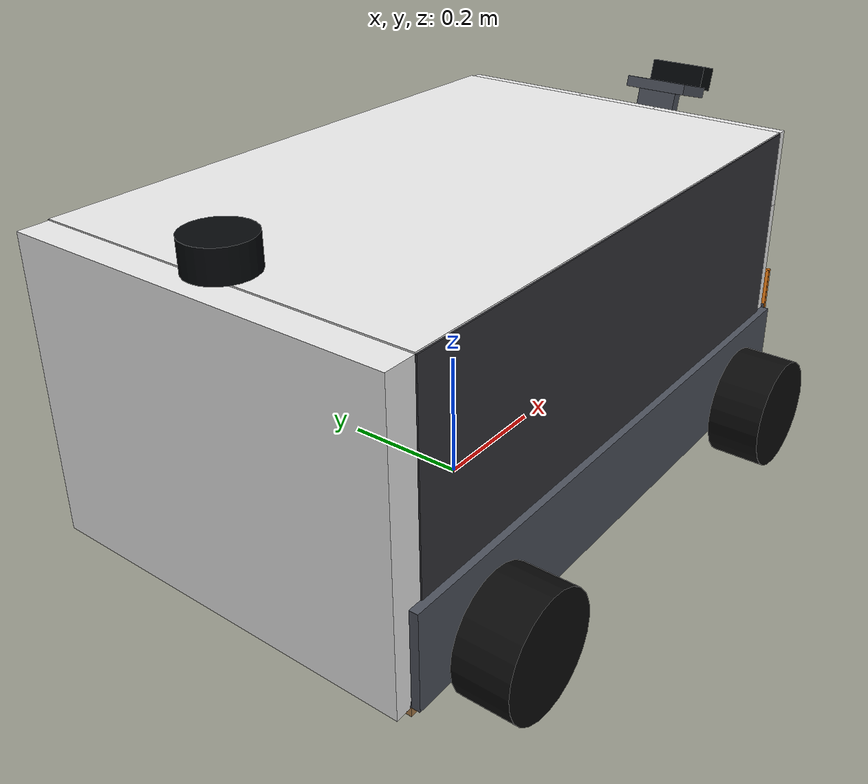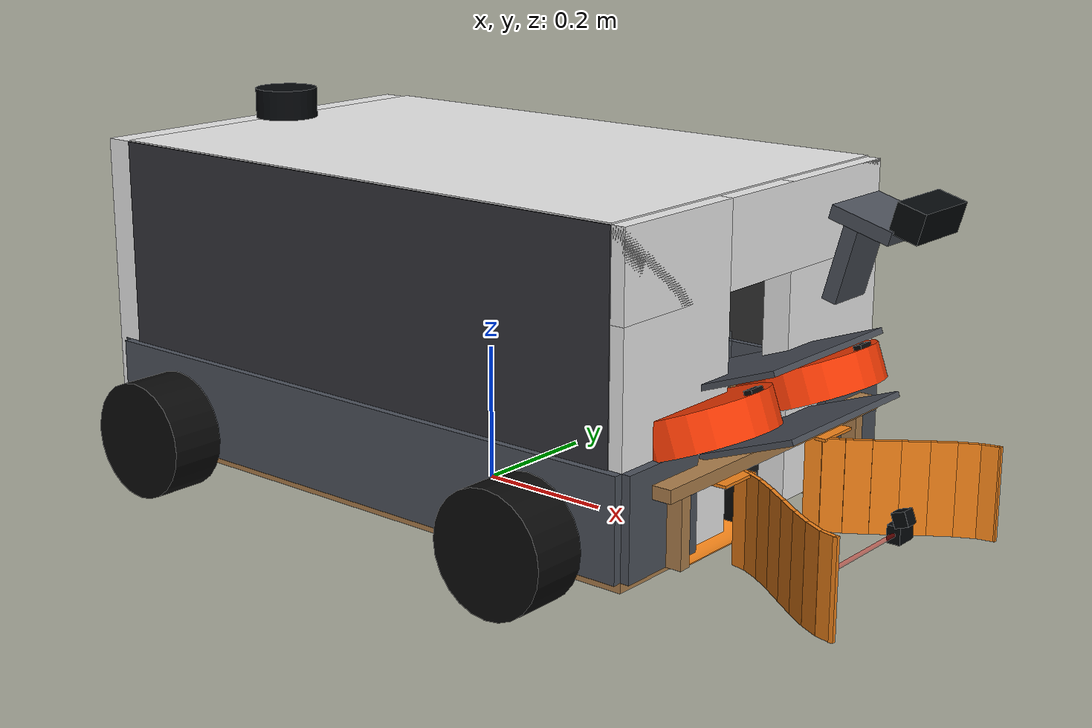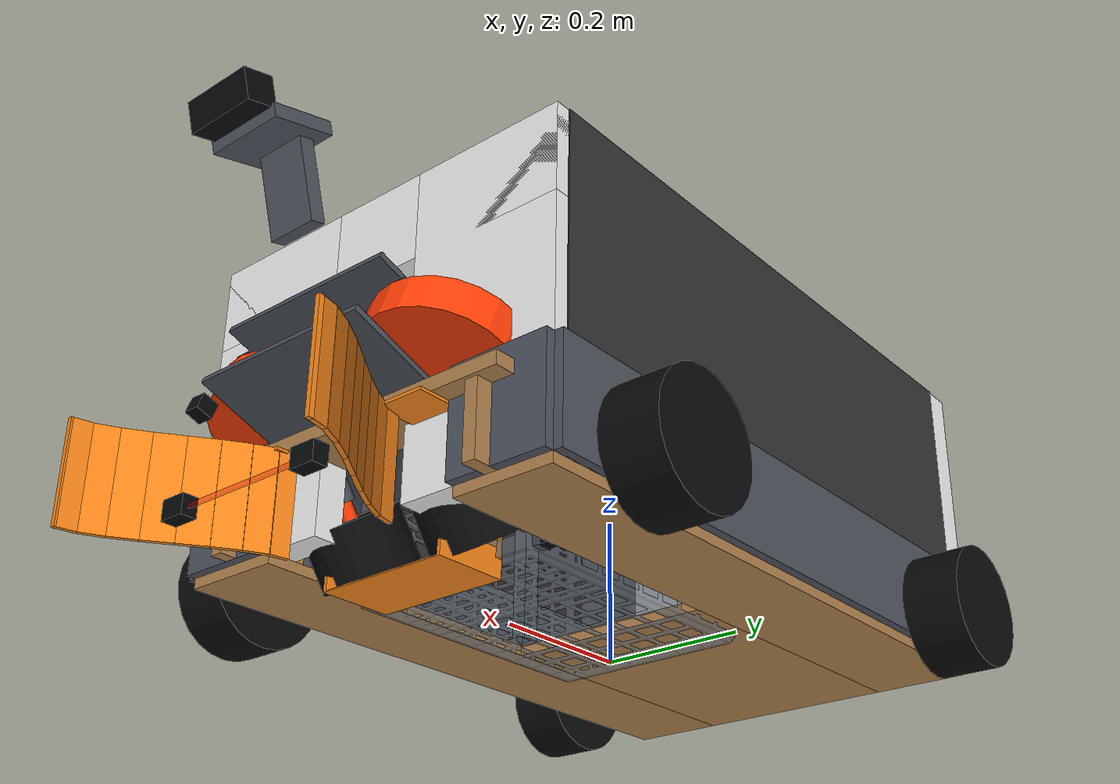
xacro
<?xml version="1.0" encoding="UTF-8"?>
<robot name="tennis_robot" xmlns:xacro="http://www.ros.org/wiki/xacro">
  <xacro:include filename="components/materials.urdf.xacro"/>
  <xacro:include filename="components/base.urdf.xacro"/>
  <xacro:include filename="components/basket.urdf.xacro"/>
  <xacro:include filename="components/battery.urdf.xacro"/>
  <xacro:include filename="components/drivetrain.urdf.xacro"/>
  <xacro:include filename="components/ros2_control.urdf.xacro"/>
  <xacro:include filename="components/lidar.urdf.xacro"/>
  <xacro:include filename="components/oak_d.urdf.xacro"/>
  <xacro:include filename="components/imu.urdf.xacro"/>
  <xacro:include filename="components/ir_beam.urdf.xacro"/>
  <xacro:include filename="components/body_panels.urdf.xacro"/>
  <xacro:include filename="components/intake_debug_camera.urdf.xacro"/>
  <xacro:include filename="components/electronics_packaging.urdf.xacro"/>
  <xacro:include filename="components/flywheel_launcher.urdf.xacro"/>
  <xacro:include filename="components/compact_mechanics.urdf.xacro"/>

  <xacro:arg name="sim_mode" default="true"/>
  <xacro:arg name="controllers_config" default="config/controllers.yaml"/>
  <!-- Packaging overlay of the ONE robot: the compact CAD machine shifts the
       complete functional chain by -100 mm. Injected by
       scripts/generate_robot_urdf.py from scripts/intake_geometry.py. -->
  <xacro:arg name="functional_shift_x" default="-0.100"/>
  <xacro:arg name="intake_cad_alignment_x" default="-0.070"/>
  <xacro:arg name="battery_center_x" default="-0.143"/>
  <xacro:arg name="enable_compact_electronics" default="true"/>
  <!-- ONE robot: the compact CAD machine. The baseline / option-a-* packaging
       variants were archived 2026-08-27; components/archive/ keeps their xacro. -->
  <xacro:arg name="enable_compact_mechanics" default="true"/>
  <xacro:arg name="enable_basket_raised_holders" default="false"/>
  <xacro:arg name="intake_parent_link" default="compact_bridge_link"/>
  <xacro:arg name="enable_intake" default="true"/>
  <xacro:arg name="enable_flywheel" default="true"/>
  <xacro:arg name="flywheel_max_vel" default="320.0"/>
  <xacro:arg name="flywheel_nip_gap" default="0.058"/>
  <xacro:arg name="basket_empty_mass" default="1.012"/>
  <xacro:arg name="basket_payload_mass" default="0.0"/>
  <xacro:arg name="basket_lift_travel" default="0.100"/>
  <xacro:arg name="basket_lift_overtravel" default="0.010"/>
  <xacro:arg name="basket_launch_tilt_rad" default="0.0"/>
  <xacro:arg name="basket_floor_thickness" default="0.006"/>
  <xacro:arg name="basket_cad_support_details" default="true"/>
  <xacro:arg name="intake_wheel_radius" default="0.062"/>
  <xacro:arg name="intake_wheel_width" default="0.073"/>
  <xacro:arg name="intake_wheel_gap" default="0.056"/>
  <xacro:arg name="intake_nip_x" default="0.540"/>
  <xacro:arg name="intake_wheel_tilt_deg" default="35.0"/>
  <xacro:arg name="intake_wheel_max_vel" default="26.3"/>
  <xacro:arg name="intake_wheel_effort" default="1.77"/>
  <!-- Physically unmeasured felt/tread friction. SWEPT bound (0.3/0.6/0.9),
       never a value chosen to make a result pass. -->
  <xacro:arg name="intake_tread_mu" default="0.6"/>
  <!-- Concept Validation Plan gates: Phase 1 = throat only (both false),
       Phase 2 = +funnel, Phase 3 = wheels+ramp, Phase 4 = full intake. -->
  <xacro:arg name="enable_funnel" default="true"/>
  <xacro:arg name="enable_ramp" default="true"/>
  <xacro:arg name="compact_handoff_ramp_mesh"
      default="package://tennis_robot/meshes/option_a_handoff_ramp.stl"/>
  <xacro:arg name="enable_assist" default="false"/>
  <xacro:arg name="enable_conveyor" default="false"/>
  <xacro:arg name="intake_assist_x" default="0.545"/>
  <xacro:arg name="intake_assist_z" default="0.050"/>
  <xacro:arg name="intake_assist_radius" default="0.030"/>
  <xacro:arg name="intake_assist_length" default="0.200"/>
  <xacro:arg name="intake_conveyor_x_bias" default="0.000"/>
  <xacro:arg name="intake_conveyor_z_bias" default="0.000"/>
  <!-- Bin v2 (docs/basket-bin-redesign-spec-el.md): sunken removable bin.
       Ground-frame heights; front edge is pinned to the jump lip (0.425). -->
  <xacro:arg name="basket_floor_front_x" default="0.42"/>
  <xacro:arg name="basket_floor_top_z" default="0.025"/>
  <xacro:arg name="basket_rear_x" default="0.02"/>
  <xacro:arg name="basket_half_width" default="0.14"/>
  <xacro:arg name="basket_wall_top_z" default="0.25"/>
  <xacro:arg name="basket_center_lip_height" default="0.010"/>
  <xacro:arg name="basket_management_run" default="0.14"/>
  <xacro:arg name="basket_management_rise" default="0.010"/>
  <xacro:arg name="basket_receiver_run" default="0.050"/>
  <xacro:arg name="basket_receiver_rise" default="0.005"/>
  <xacro:arg name="basket_hood_rear_overhang" default="0.040"/>
  <xacro:arg name="basket_hood_rear_clearance_z" default="0.120"/>
  <xacro:arg name="basket_hood_front_clearance_z" default="0.135"/>

  <xacro:property name="chassis_x" value="0.92"/>
  <xacro:property name="chassis_y" value="0.58"/>
  <xacro:property name="chassis_z" value="0.014"/>
  <xacro:property name="chassis_mass" value="7.2"/>
  <!-- base_link is the chassis plate centre. The plate top is 52 mm above
       ground, below the 85 mm motor-shaft/wheel-axle centreline. -->
  <xacro:property name="base_link_height" value="0.045"/>
  <xacro:property name="functional_shift_x" value="${float($(arg functional_shift_x))}"/>
  <xacro:property name="intake_cad_alignment_x" value="${float($(arg intake_cad_alignment_x))}"/>

  <xacro:property name="wheel_base_x" value="0.33"/>  <!-- rear at -x, front at +x; wheelbase = 0.66 m -->
  <xacro:property name="wheel_y" value="0.35"/>
  <xacro:property name="wheel_radius" value="0.085"/>  <!-- 170 mm diameter (HPI Dirt Buster Block) -->
  <xacro:property name="wheel_z" value="${wheel_radius - base_link_height}"/>
  <xacro:property name="wheel_width" value="0.08"/>
  <xacro:property name="wheel_mass" value="0.25"/>
  <xacro:property name="wheel_separation" value="${2.0 * wheel_y}"/>
  <xacro:property name="motor_y" value="${chassis_y / 2.0 - 0.05}"/>
  <xacro:property name="motor_radius" value="0.03"/>
  <xacro:property name="motor_length" value="0.10"/>

  <xacro:property name="intake_wheel_radius" value="${float($(arg intake_wheel_radius))}"/>
  <xacro:property name="intake_wheel_gap" value="${float($(arg intake_wheel_gap))}"/>
  <xacro:property name="intake_nip_x" value="${float($(arg intake_nip_x)) + functional_shift_x + intake_cad_alignment_x}"/>
  <xacro:property name="intake_wheel_tilt_rad" value="${float($(arg intake_wheel_tilt_deg)) * 0.017453292519943295}"/>
  <xacro:property name="intake_wheel_max_vel" value="${float($(arg intake_wheel_max_vel))}"/>
  <xacro:property name="intake_wheel_effort" value="${float($(arg intake_wheel_effort))}"/>
  <!-- Wheel centre offset from the corridor centreline. -->
  <xacro:property name="intake_wheel_y" value="${intake_wheel_gap / 2.0 + intake_wheel_radius}"/>
  <xacro:property name="intake_wheel_height" value="${float($(arg intake_wheel_width))}"/>
  <xacro:property name="intake_wheel_z" value="${0.070 - base_link_height}"/>
  <xacro:property name="intake_assist_x" value="${float($(arg intake_assist_x))}"/>
  <xacro:property name="intake_assist_z" value="${float($(arg intake_assist_z))}"/>
  <xacro:property name="intake_assist_radius" value="${float($(arg intake_assist_radius))}"/>
  <xacro:property name="intake_assist_length" value="${float($(arg intake_assist_length))}"/>
  <xacro:property name="intake_conveyor_x_bias" value="${float($(arg intake_conveyor_x_bias))}"/>
  <xacro:property name="intake_conveyor_z_bias" value="${float($(arg intake_conveyor_z_bias))}"/>
  <xacro:property name="intake_conveyor_radius" value="0.025"/>
  <xacro:property name="intake_conveyor_length" value="0.200"/>
  <xacro:property name="scooper_pitch" value="0.1745"/>  <!-- 10 degrees; funnel-cheek tilt -->

  <xacro:property name="lidar_scan_plane_z_ground" value="0.5535"/>
  <xacro:property name="lidar_sensor_scan_offset" value="0.035"/>
  <xacro:property name="lidar_mount_z"
      value="${lidar_scan_plane_z_ground - base_link_height - lidar_sensor_scan_offset}"/>
  <xacro:property name="lidar_xyz" value="-0.42 0 ${lidar_mount_z}"/>
  <xacro:property name="lidar_rpy" value="0 0 0"/>  <!-- level chassis: horizontal scan plane -->
       The literal below is a CAD-frame X: functional_shift_x (-0.100 on the
       compact variant) converts it to base_link. 0.790 IS the CAD
       nose_front_x, so compact lands at base_link 0.690, next to the cheek
       mouth which compact_mechanics hardcodes at base_link 0.705 (CAD 805).
       Writing 0.690 here would double-shift it to 0.590. -->
  <xacro:property name="camera_xyz" value="${0.790 + functional_shift_x} 0 0.443"/>
  <xacro:property name="camera_rpy" value="0 0.273 0"/>  <!-- forward-down tilt ~15.6deg; preserves the old world aim (0.22 cam + 0.053 chassis pitch) now that the chassis is level -->
  <xacro:property name="sensor_update_rate" value="31.25"/>

  <xacro:property name="intake_debug_camera_xyz" value="${0.78 + functional_shift_x} 0 0.06"/>
  <xacro:property name="intake_debug_camera_rpy" value="0 0.339 3.14159"/>

  <xacro:property name="ir_x" value="${0.720 + functional_shift_x}"/>
  <xacro:property name="ir_y" value="0.105"/>
  <xacro:property name="ir_z" value="-0.005"/>
  <xacro:property name="basket_ir_x" value="${float($(arg basket_floor_front_x)) - float($(arg basket_management_run)) / 2.0 + functional_shift_x}"/>
  <xacro:property name="basket_ir_y" value="0.105"/>
  <xacro:property name="basket_ir_z" value="${float($(arg basket_floor_top_z)) + float($(arg basket_management_rise)) / 2.0 + 0.045 - base_link_height}"/>

  <xacro:property name="max_linear_acceleration" value="2.0"/>
  <xacro:property name="max_angular_acceleration" value="4.0"/>

  <xacro:tennis_robot_base
      chassis_x="${chassis_x}"
      chassis_y="${chassis_y}"
      chassis_z="${chassis_z}"
      base_link_height="${base_link_height}"
      chassis_mass="${chassis_mass}"
      entry_beam_x="${ir_x}"
      entry_beam_z="${ir_z}"
      entry_beam_width="${2.0 * ir_y}"/>

  <!-- Motors are fixed to the chassis top. Each shaft shares its x/z centre
       with the corresponding wheel joint; only y differs along the shaft. -->
  <xacro:drive_motor side="rear_left" y="${motor_y}" motor_x="-${wheel_base_x}"
      shaft_z="${wheel_z}" radius="${motor_radius}" length="${motor_length}" mass="0.65"/>
  <xacro:drive_motor side="rear_right" y="-${motor_y}" motor_x="-${wheel_base_x}"
      shaft_z="${wheel_z}" radius="${motor_radius}" length="${motor_length}" mass="0.65"/>
  <xacro:drive_motor side="front_left" y="${motor_y}" motor_x="${wheel_base_x}"
      shaft_z="${wheel_z}" radius="${motor_radius}" length="${motor_length}" mass="0.65"/>
  <xacro:drive_motor side="front_right" y="-${motor_y}" motor_x="${wheel_base_x}"
      shaft_z="${wheel_z}" radius="${motor_radius}" length="${motor_length}" mass="0.65"/>

  <xacro:drive_wheel
      side="rear_left"
      y="${wheel_y}"
      wheel_x="-${wheel_base_x}"
      wheel_z="${wheel_z}"
      radius="${wheel_radius}"
      width="${wheel_width}"
      mass="${wheel_mass}"/>

  <xacro:drive_wheel
      side="rear_right"
      y="-${wheel_y}"
      wheel_x="-${wheel_base_x}"
      wheel_z="${wheel_z}"
      radius="${wheel_radius}"
      width="${wheel_width}"
      mass="${wheel_mass}"/>

  <xacro:drive_wheel
      side="front_left"
      y="${wheel_y}"
      wheel_x="${wheel_base_x}"
      wheel_z="${wheel_z}"
      radius="${wheel_radius}"
      width="${wheel_width}"
      mass="${wheel_mass}"/>

  <xacro:drive_wheel
      side="front_right"
      y="-${wheel_y}"
      wheel_x="${wheel_base_x}"
      wheel_z="${wheel_z}"
      radius="${wheel_radius}"
      width="${wheel_width}"
      mass="${wheel_mass}"/>

  <!-- The compact bridge is the real load path for the intake pods and the
       launcher cradle.  It must exist before those child joints are emitted. -->
  <xacro:if value="$(arg enable_compact_mechanics)">
    <xacro:compact_plywood_bridge parent="base_link" base_link_height="${base_link_height}"/>
    <xacro:compact_basket_fixed_rails parent="base_link"
        x_shift="${functional_shift_x}" base_link_height="${base_link_height}"/>
    <xacro:compact_fixed_entry_hood parent="base_link"
        x_shift="${functional_shift_x}" base_link_height="${base_link_height}"/>
    <xacro:if value="$(arg enable_basket_raised_holders)">
      <xacro:compact_basket_raised_holders parent="base_link"
          x_shift="${functional_shift_x}" base_link_height="${base_link_height}"/>
    </xacro:if>
  </xacro:if>

  <!-- Intake assembly.  In compact it is bridge-mounted and uses the measured
       CAD cheeks/ramp; older study variants retain their historical funnel. -->
  <xacro:if value="$(arg enable_intake)">
    <!-- Left wheel drives ω<0 / right ω>0 (opposite signs, commanded by
         intake_wheel_velocity_controller) so both inner faces move rearward. -->
    <xacro:intake_side_wheel
        side="left"
        y="${intake_wheel_y}"
        nip_x="${intake_nip_x}"
        wheel_z="${intake_wheel_z}"
        tilt_rad="${intake_wheel_tilt_rad}"
        radius="${intake_wheel_radius}"
        height="${intake_wheel_height}"
        max_vel="${intake_wheel_max_vel}"
        effort="${intake_wheel_effort}"
        tread_mu="${float($(arg intake_tread_mu))}"
        mass="0.20"
        parent="$(arg intake_parent_link)"
        sensor_index="0"/>
    <xacro:intake_side_wheel
        side="right"
        y="${-intake_wheel_y}"
        nip_x="${intake_nip_x}"
        wheel_z="${intake_wheel_z}"
        tilt_rad="${intake_wheel_tilt_rad}"
        radius="${intake_wheel_radius}"
        height="${intake_wheel_height}"
        max_vel="${intake_wheel_max_vel}"
        effort="${intake_wheel_effort}"
        tread_mu="${float($(arg intake_tread_mu))}"
        mass="0.20"
        parent="$(arg intake_parent_link)"
        sensor_index="1"/>

    <xacro:if value="$(arg enable_compact_mechanics)">
      <xacro:compact_intake_static_structure parent="compact_bridge_link"
          base_link_height="${base_link_height}"
          enable_cheeks="$(arg enable_funnel)" enable_ramp="$(arg enable_ramp)"
          ramp_mesh="$(arg compact_handoff_ramp_mesh)"/>
    </xacro:if>
</xacro:if>
  <xacro:if value="$(arg enable_assist)">
    <xacro:intake_assist_roller
        parent="base_link"
        x="${intake_assist_x + functional_shift_x}"
        z="${intake_assist_z}"
        radius="${intake_assist_radius}"
        length="${intake_assist_length}"
        mass="0.20"/>
  </xacro:if>
  <xacro:if value="$(arg enable_conveyor)">
    <xacro:intake_ramp_conveyor_roller
        name="intake_conveyor_front"
        parent="base_link"
        x="${0.525 + intake_conveyor_x_bias + functional_shift_x}"
        z="${0.051 + intake_conveyor_z_bias}"
        radius="${intake_conveyor_radius}"
        length="${intake_conveyor_length}"
        mass="0.14"/>
    <xacro:intake_ramp_conveyor_roller
        name="intake_conveyor_mid"
        parent="base_link"
        x="${0.490 + intake_conveyor_x_bias + functional_shift_x}"
        z="${0.067 + intake_conveyor_z_bias}"
        radius="${intake_conveyor_radius}"
        length="${intake_conveyor_length}"
        mass="0.14"/>
    <xacro:intake_ramp_conveyor_roller
        name="intake_conveyor_rear"
        parent="base_link"
        x="${0.455 + intake_conveyor_x_bias + functional_shift_x}"
        z="${0.101 + intake_conveyor_z_bias}"
        radius="${intake_conveyor_radius}"
        length="${intake_conveyor_length}"
        mass="0.14"/>
  </xacro:if>
  <xacro:ball_basket
      parent="base_link"
      floor_front_x="${float($(arg basket_floor_front_x))}"
      floor_top_z_ground="${float($(arg basket_floor_top_z))}"
      rear_x="${float($(arg basket_rear_x))}"
      half_width="${float($(arg basket_half_width))}"
      wall_top_z_ground="${float($(arg basket_wall_top_z))}"
      center_lip_height="${float($(arg basket_center_lip_height))}"
      management_run="${float($(arg basket_management_run))}"
      management_rise="${float($(arg basket_management_rise))}"
      receiver_run="${float($(arg basket_receiver_run))}"
      receiver_rise="${float($(arg basket_receiver_rise))}"
      hood_rear_overhang="${float($(arg basket_hood_rear_overhang))}"
      hood_rear_clearance_z_ground="${float($(arg basket_hood_rear_clearance_z))}"
      hood_front_clearance_z_ground="${float($(arg basket_hood_front_clearance_z))}"
      x_shift="${functional_shift_x}"
      lift_travel="${float($(arg basket_lift_travel))}"
      lift_overtravel="${float($(arg basket_lift_overtravel))}"
      empty_mass="${float($(arg basket_empty_mass))}"
      payload_mass="${float($(arg basket_payload_mass))}"
      launch_tilt_rad="${float($(arg basket_launch_tilt_rad))}"
      floor_thickness="${float($(arg basket_floor_thickness))}"
      cad_support_details="$(arg basket_cad_support_details)"/>
  <xacro:battery_pack parent="base_link"
      center_x="${float($(arg battery_center_x))}"/>

  <xacro:if value="$(arg enable_compact_electronics)">
    <xacro:compact_electronics_packaging
        parent="base_link" base_link_height="${base_link_height}"/>
  </xacro:if>

  <xacro:if value="$(arg enable_flywheel)">
    <xacro:if value="$(arg enable_compact_mechanics)">
      <xacro:compact_cad_flywheel_launcher parent="compact_bridge_link"
          base_link_height="${base_link_height}"
          nip_gap="${float($(arg flywheel_nip_gap))}"
          max_vel="${float($(arg flywheel_max_vel))}"/>
    </xacro:if>
</xacro:if>

  <xacro:rplidar_c1_mount
      parent="base_link"
      link_name="lidar_link"
      xyz="${lidar_xyz}"
      rpy="${lidar_rpy}"
      mount_z="${lidar_mount_z}"
      scan_offset_z="${lidar_sensor_scan_offset}"
      update_rate="${sensor_update_rate}"/>

  <xacro:oak_d_lite_mount
      parent="base_link"
      link_name="camera_link"
      xyz="${camera_xyz}"
      rpy="${camera_rpy}"
      update_rate="${sensor_update_rate}"/>

  <!-- Sim-only: no real-hardware equivalent. -->
  <xacro:if value="$(arg sim_mode)">
    <xacro:intake_debug_camera
        parent="base_link"
        link_name="intake_debug_camera_link"
        xyz="${intake_debug_camera_xyz}"
        rpy="${intake_debug_camera_rpy}"
        update_rate="${sensor_update_rate}"/>
  </xacro:if>

  <!-- MPU6050 IMU near the chassis centre, axes aligned with base_link. Mainly
       used for yaw rate, which wheel odometry mis-estimates in skid-steer. -->
  <xacro:mpu6050_imu
      parent="base_link"
      link_name="imu_link"
      xyz="-0.05 0 0.012"
      rpy="0 0 0"
      update_rate="100"
      topic="/gz/imu"/>

  <xacro:ir_beam_sensor
      parent="base_link"
      link_name="ir_left_link"
      joint_name="ir_left_joint"
      xyz="${ir_x} -${ir_y} ${ir_z}"
      rpy="0 0 1.5708"
      topic="/gz/ir_left"
      update_rate="${sensor_update_rate}"/>
  <xacro:ir_beam_sensor
      parent="base_link"
      link_name="ir_right_link"
      joint_name="ir_right_joint"
      xyz="${ir_x} ${ir_y} ${ir_z}"
      rpy="0 0 -1.5708"
      topic="/gz/ir_right"
      update_rate="${sensor_update_rate}"/>
  <xacro:ir_beam_sensor
      parent="base_link"
      link_name="basket_ir_left_link"
      joint_name="basket_ir_left_joint"
      xyz="${basket_ir_x} -${basket_ir_y} ${basket_ir_z}"
      rpy="0 0 1.5708"
      topic="/gz/basket_ir_left"
      update_rate="${sensor_update_rate}"/>
  <xacro:ir_beam_sensor
      parent="base_link"
      link_name="basket_ir_right_link"
      joint_name="basket_ir_right_joint"
      xyz="${basket_ir_x} ${basket_ir_y} ${basket_ir_z}"
      rpy="0 0 -1.5708"
      topic="/gz/basket_ir_right"
      update_rate="${sensor_update_rate}"/>

  <xacro:tennis_robot_ros2_control
      sim_mode="$(arg sim_mode)"
      controllers_config="$(arg controllers_config)"
      intake_max_vel="${intake_wheel_max_vel}"
      enable_intake="$(arg enable_intake)"
      enable_flywheel="$(arg enable_flywheel)"
      flywheel_max_vel="${float($(arg flywheel_max_vel))}"
      basket_lift_travel="${float($(arg basket_lift_travel))}"
      enable_assist="$(arg enable_assist)"
      enable_conveyor="$(arg enable_conveyor)"/>

  <xacro:robot_body_panels parent="base_link" chassis_z="${chassis_z}"/>
</robot>

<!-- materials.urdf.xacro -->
<robot xmlns:xacro="http://www.ros.org/wiki/xacro">
  <material name="plywood">
    <color rgba="0.68 0.50 0.30 1"/>
  </material>
  <material name="anthracite">
    <color rgba="0.18 0.19 0.22 1"/>
  </material>
  <material name="intake_orange">
    <color rgba="0.96 0.52 0.10 1"/>
  </material>
  <material name="safety_orange">
    <color rgba="1.0 0.24 0.02 1"/>
  </material>
  <material name="mount_gray">
    <color rgba="0.30 0.32 0.36 1"/>
  </material>
  <material name="basket_gray">
    <color rgba="0.42 0.45 0.48 0.65"/>
  </material>
  <material name="rubber_black">
    <color rgba="0.04 0.04 0.04 1"/>
  </material>
  <material name="sensor_black">
    <color rgba="0.02 0.03 0.04 1"/>
  </material>
  <material name="electronics_blue">
    <color rgba="0.08 0.28 0.62 1"/>
  </material>
  <material name="body_dark_grey">
    <color rgba="0.20 0.20 0.22 1"/>
  </material>
  <material name="ir_beam_red">
    <color rgba="1.0 0.05 0.02 0.35"/>
  </material>
</robot>

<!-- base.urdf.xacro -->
<robot xmlns:xacro="http://www.ros.org/wiki/xacro">
  <xacro:macro name="box_inertial" params="mass x y z">
    <inertial>
      <mass value="${mass}"/>
      <inertia
          ixx="${mass * (y*y + z*z) / 12.0}" ixy="0" ixz="0"
          iyy="${mass * (x*x + z*z) / 12.0}" iyz="0"
          izz="${mass * (x*x + y*y) / 12.0}"/>
    </inertial>
  </xacro:macro>

  <xacro:macro name="cylinder_inertial" params="mass radius length axis">
    <inertial>
      <mass value="${mass}"/>
      <xacro:if value="${axis == 'y'}">
        <inertia
            ixx="${mass * (3.0 * radius * radius + length * length) / 12.0}" ixy="0" ixz="0"
            iyy="${0.5 * mass * radius * radius}" iyz="0"
            izz="${mass * (3.0 * radius * radius + length * length) / 12.0}"/>
      </xacro:if>
      <xacro:unless value="${axis == 'y'}">
        <inertia
            ixx="${mass * (3.0 * radius * radius + length * length) / 12.0}" ixy="0" ixz="0"
            iyy="${mass * (3.0 * radius * radius + length * length) / 12.0}" iyz="0"
            izz="${0.5 * mass * radius * radius}"/>
      </xacro:unless>
    </inertial>
  </xacro:macro>

  <xacro:macro name="tennis_robot_base"
               params="chassis_x chassis_y chassis_z base_link_height chassis_mass entry_beam_x entry_beam_z entry_beam_width">
    <link name="base_footprint"/>

    <joint name="base_footprint_joint" type="fixed">
      <parent link="base_footprint"/>
      <child link="base_link"/>
      <!-- base_footprint is the ground plane. base_link is the centre of the
           chassis plate, deliberately below the motor/axle centreline. -->
      <origin xyz="0 0 ${base_link_height}" rpy="0 0 0"/>
    </joint>

    <link name="base_link">
      <xacro:box_inertial mass="${chassis_mass}" x="${chassis_x}" y="${chassis_y}" z="${chassis_z}"/>
      <collision name="chassis_left_col">
        <origin xyz="0 0.22 0" rpy="0 0 0"/>
        <geometry><box size="${chassis_x} 0.14 ${chassis_z}"/></geometry>
      </collision>
      <collision name="chassis_right_col">
        <origin xyz="0 -0.22 0" rpy="0 0 0"/>
        <geometry><box size="${chassis_x} 0.14 ${chassis_z}"/></geometry>
      </collision>
      <collision name="chassis_rear_col">
        <origin xyz="-0.225 0 0" rpy="0 0 0"/>
        <geometry><box size="0.47 0.30 ${chassis_z}"/></geometry>
      </collision>
      <visual name="chassis_left_vis">
        <origin xyz="0 0.22 0" rpy="0 0 0"/>
        <geometry><box size="${chassis_x} 0.14 ${chassis_z}"/></geometry>
        <material name="plywood"/>
      </visual>
      <visual name="chassis_right_vis">
        <origin xyz="0 -0.22 0" rpy="0 0 0"/>
        <geometry><box size="${chassis_x} 0.14 ${chassis_z}"/></geometry>
        <material name="plywood"/>
      </visual>
      <visual name="chassis_rear_vis">
        <origin xyz="-0.225 0 0" rpy="0 0 0"/>
        <geometry><box size="0.47 0.30 ${chassis_z}"/></geometry>
        <material name="plywood"/>
      </visual>

      <visual name="front_left_cheek_vis">
        <origin xyz="${chassis_x / 2.0} ${0.30 / 2.0 + (chassis_y - 0.30) / 4.0} 0.077" rpy="0 0 0"/>
        <geometry><box size="0.025 ${(chassis_y - 0.30) / 2.0} 0.14"/></geometry>
        <material name="mount_gray"/>
      </visual>
      <visual name="front_right_cheek_vis">
        <origin xyz="${chassis_x / 2.0} ${-(0.30 / 2.0 + (chassis_y - 0.30) / 4.0)} 0.077" rpy="0 0 0"/>
        <geometry><box size="0.025 ${(chassis_y - 0.30) / 2.0} 0.14"/></geometry>
        <material name="mount_gray"/>
      </visual>
      <visual name="rear_wall_vis">
        <origin xyz="${-chassis_x / 2.0} 0 0.077" rpy="0 0 0"/>
        <geometry><box size="0.025 ${chassis_y} 0.14"/></geometry>
        <material name="mount_gray"/>
      </visual>
      <visual name="left_wall_vis">
        <origin xyz="0 ${chassis_y / 2.0} 0.077" rpy="0 0 0"/>
        <geometry><box size="${chassis_x} 0.025 0.14"/></geometry>
        <material name="mount_gray"/>
      </visual>
      <visual name="right_wall_vis">
        <origin xyz="0 ${-chassis_y / 2.0} 0.077" rpy="0 0 0"/>
        <geometry><box size="${chassis_x} 0.025 0.14"/></geometry>
        <material name="mount_gray"/>
      </visual>
      <visual name="rear_left_axle_bracket_vis">
        <origin xyz="-0.33 0.24 ${0.5 * chassis_z + 0.009}" rpy="0 0 0"/>
        <geometry><box size="0.065 0.060 0.018"/></geometry>
        <material name="mount_gray"/>
      </visual>
      <visual name="rear_right_axle_bracket_vis">
        <origin xyz="-0.33 -0.24 ${0.5 * chassis_z + 0.009}" rpy="0 0 0"/>
        <geometry><box size="0.065 0.060 0.018"/></geometry>
        <material name="mount_gray"/>
      </visual>
      <visual name="front_left_axle_bracket_vis">
        <origin xyz="0.33 0.24 ${0.5 * chassis_z + 0.009}" rpy="0 0 0"/>
        <geometry><box size="0.065 0.060 0.018"/></geometry>
        <material name="mount_gray"/>
      </visual>
      <visual name="front_right_axle_bracket_vis">
        <origin xyz="0.33 -0.24 ${0.5 * chassis_z + 0.009}" rpy="0 0 0"/>
        <geometry><box size="0.065 0.060 0.018"/></geometry>
        <material name="mount_gray"/>
      </visual>
      <visual name="elec_vis">
        <origin xyz="-0.36 0 0.067" rpy="0 0 0"/>
        <geometry><box size="0.18 0.26 0.12"/></geometry>
        <material name="anthracite"/>
      </visual>
      <visual name="ir_beam_line_vis">
        <origin xyz="${entry_beam_x} 0 ${entry_beam_z}" rpy="1.5708 0 0"/>
        <geometry><cylinder radius="0.003" length="${entry_beam_width}"/></geometry>
        <material name="ir_beam_red"/>
      </visual>
    </link>

    <gazebo reference="base_link">
      <material>Gazebo/Wood</material>
    </gazebo>
  </xacro:macro>
</robot>

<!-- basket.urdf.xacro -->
<robot xmlns:xacro="http://www.ros.org/wiki/xacro">
  <xacro:macro name="basket_wire" params="name xyz size">
    <visual name="${name}">
      <origin xyz="${xyz}" rpy="0 0 0"/>
      <geometry><box size="${size}"/></geometry>
      <material name="basket_gray"/>
    </visual>
  </xacro:macro>

  <xacro:macro name="basket_wire_rotated" params="name xyz rpy size">
    <visual name="${name}">
      <origin xyz="${xyz}" rpy="${rpy}"/>
      <geometry><box size="${size}"/></geometry>
      <material name="basket_gray"/>
    </visual>
  </xacro:macro>

  <xacro:macro name="ball_basket"
      params="parent floor_front_x floor_top_z_ground rear_x half_width wall_top_z_ground center_lip_height management_run management_rise receiver_run receiver_rise hood_rear_overhang hood_rear_clearance_z_ground hood_front_clearance_z_ground x_shift:=0.0 lift_travel:=0.100 lift_overtravel:=0.010 empty_mass:=0.01 payload_mass:=0.0 launch_tilt_rad:=0.0 launch_pivot_x:=0.470 launch_pivot_z_ground:=0.040 floor_thickness:=0.005 cad_support_details:=false">
    <xacro:property name="floor_top" value="${floor_top_z_ground - base_link_height}"/>
    <xacro:property name="wall_top" value="${wall_top_z_ground - base_link_height}"/>
    <!-- Thin skinned bin: 5 mm floor (exterior bottom = floor_top - 0.005,
         the robot's lowest point), 10 mm wall frames. -->
    <xacro:property name="wall_thickness" value="0.010"/>
    <xacro:property name="bin_length" value="${floor_front_x - rear_x}"/>
    <xacro:property name="wall_height" value="${wall_top - floor_top}"/>
    <xacro:property name="wall_centre_z" value="${(wall_top + floor_top) / 2.0}"/>
    <xacro:property name="entry_half_width" value="0.090"/>
    <xacro:property name="front_guard_width" value="${half_width - entry_half_width}"/>
    <xacro:property name="front_guard_height" value="0.020"/>
    <xacro:property name="front_guard_centre_z" value="${floor_top + front_guard_height / 2.0}"/>
    <xacro:property name="management_rear_x" value="${floor_front_x - management_run}"/>
    <xacro:property name="management_pitch" value="${-atan2(management_rise, management_run)}"/>
    <xacro:property name="management_length" value="${sqrt(management_run * management_run + management_rise * management_rise)}"/>
    <xacro:property name="management_top_mid_x" value="${(floor_front_x + management_rear_x) / 2.0}"/>
    <xacro:property name="management_top_mid_z" value="${floor_top + management_rise / 2.0}"/>
    <xacro:property name="management_centre_x" value="${management_top_mid_x - sin(management_pitch) * floor_thickness / 2.0}"/>
    <xacro:property name="management_centre_z" value="${management_top_mid_z - cos(management_pitch) * floor_thickness / 2.0}"/>
    <!-- A narrow front receiver continues the management tray toward the
         wheel pair. The ball crosses a short free-flight gap, lands on this
         surface, then rolls rearward into the main bin. -->
    <xacro:property name="receiver_rear_top_z" value="${floor_top + management_rise}"/>
    <xacro:property name="receiver_front_x" value="${floor_front_x + receiver_run}"/>
    <xacro:property name="receiver_pitch" value="${-atan2(receiver_rise, receiver_run)}"/>
    <xacro:property name="receiver_length" value="${sqrt(receiver_run * receiver_run + receiver_rise * receiver_rise)}"/>
    <xacro:property name="receiver_top_mid_x" value="${floor_front_x + receiver_run / 2.0}"/>
    <xacro:property name="receiver_top_mid_z" value="${receiver_rear_top_z + receiver_rise / 2.0}"/>
    <xacro:property name="receiver_centre_x" value="${receiver_top_mid_x - sin(receiver_pitch) * floor_thickness / 2.0}"/>
    <xacro:property name="receiver_centre_z" value="${receiver_top_mid_z - cos(receiver_pitch) * floor_thickness / 2.0}"/>
    <xacro:property name="receiver_half_width" value="${entry_half_width}"/>
    <xacro:property name="confirmation_beam_x" value="${management_top_mid_x}"/>
    <!-- Matches basket_ir_z in tennis_robot.urdf.xacro: above court-ball top
         (0.066) so the beam cannot see ground balls through the mesh. -->
    <xacro:property name="confirmation_beam_z" value="${management_top_mid_z + 0.045}"/>
    <xacro:property name="hood_rear_x" value="${floor_front_x - hood_rear_overhang}"/>
    <xacro:property name="hood_run" value="${receiver_front_x - hood_rear_x}"/>
    <xacro:property name="hood_rise" value="${hood_front_clearance_z_ground - hood_rear_clearance_z_ground}"/>
    <xacro:property name="hood_pitch" value="${-atan2(hood_rise, hood_run)}"/>
    <xacro:property name="hood_length" value="${sqrt(hood_run * hood_run + hood_rise * hood_rise)}"/>
    <xacro:property name="hood_under_mid_x" value="${(hood_rear_x + receiver_front_x) / 2.0}"/>
    <xacro:property name="hood_under_mid_z" value="${(hood_rear_clearance_z_ground + hood_front_clearance_z_ground) / 2.0 - base_link_height}"/>
    <xacro:property name="hood_centre_x" value="${hood_under_mid_x + sin(hood_pitch) * floor_thickness / 2.0}"/>
    <xacro:property name="hood_centre_z" value="${hood_under_mid_z + cos(hood_pitch) * floor_thickness / 2.0}"/>
    <xacro:property name="hood_side_top_z" value="${hood_rear_clearance_z_ground - base_link_height + hood_rise * (receiver_top_mid_x - hood_rear_x) / hood_run}"/>
    <xacro:property name="hood_side_mid_z" value="${(receiver_top_mid_z + hood_side_top_z) / 2.0}"/>
    <xacro:property name="hood_side_height" value="${hood_side_top_z - receiver_top_mid_z}"/>
    <xacro:property name="basket_mass" value="${empty_mass + payload_mass}"/>
    <xacro:property name="basket_com_x" value="${0.209460 if cad_support_details else (floor_front_x + rear_x) / 2.0}"/>
    <xacro:property name="basket_com_z" value="${0.091481 - base_link_height if cad_support_details else floor_top + 0.45 * wall_height}"/>
    <joint name="basket_joint" type="prismatic">
      <parent link="${parent}"/>
      <child link="basket_guide_path_link"/>
      <origin xyz="${x_shift} 0 0" rpy="0 0 0"/>
      <axis xyz="0 0 1"/>
      <limit lower="${-lift_overtravel}" upper="${lift_travel}" effort="120.0" velocity="0.12"/>
      <dynamics damping="1.0" friction="0.0"/>
    </joint>
    <link name="basket_guide_path_link"/>
    <joint name="basket_launch_pose_joint" type="fixed">
      <parent link="basket_guide_path_link"/>
      <child link="basket_link"/>
      <!-- T(pivot) * R_y(tilt) * T(-pivot), collapsed into one URDF origin
           so the entire basket rotates about the CAD pivot without a massless
           intermediary physical link. -->
      <origin xyz="${launch_pivot_x - (cos(launch_tilt_rad) * launch_pivot_x + sin(launch_tilt_rad) * (launch_pivot_z_ground - base_link_height))} 0 ${launch_pivot_z_ground - base_link_height - (-sin(launch_tilt_rad) * launch_pivot_x + cos(launch_tilt_rad) * (launch_pivot_z_ground - base_link_height))}"
              rpy="0 ${launch_tilt_rad} 0"/>
    </joint>
    <link name="basket_link">
      <inertial>
        <origin xyz="${basket_com_x} 0 ${basket_com_z}" rpy="0 0 0"/>
        <mass value="${basket_mass}"/>
        <inertia
            ixx="${basket_mass * ((2.0 * half_width) * (2.0 * half_width) + wall_height * wall_height) / 12.0}"
            ixy="0" ixz="0"
            iyy="${basket_mass * (bin_length * bin_length + wall_height * wall_height) / 12.0}"
            iyz="0"
            izz="${basket_mass * (bin_length * bin_length + (2.0 * half_width) * (2.0 * half_width)) / 12.0}"/>
      </inertial>

      <xacro:if value="${cad_support_details}">
        <collision name="compact_relieved_bin_col">
          <origin xyz="0 0 ${-base_link_height}" rpy="0 0 0"/>
          <geometry><mesh filename="package://tennis_robot/meshes/compact_relieved_bin.stl" scale="0.001 0.001 0.001"/></geometry>
        </collision>
        <visual name="compact_relieved_bin_vis">
          <origin xyz="0 0 ${-base_link_height}" rpy="0 0 0"/>
          <geometry><mesh filename="package://tennis_robot/meshes/compact_relieved_bin.stl" scale="0.001 0.001 0.001"/></geometry>
          <material name="basket_gray"/>
        </visual>
      </xacro:if>
      <xacro:unless value="${cad_support_details}">
      <collision name="basket_floor_col">
        <origin xyz="${(floor_front_x + rear_x) / 2.0} 0 ${floor_top - floor_thickness / 2.0}" rpy="0 0 0"/>
        <geometry><box size="${bin_length} ${2.0 * half_width} ${floor_thickness}"/></geometry>
      </collision>
      <!-- Visuals are an open 40 mm wire grid like a tennis training hopper.
           Physics keeps a continuous collision envelope because the 66 mm
           ball cannot pass through the grid openings. -->
      <xacro:basket_wire name="basket_floor_long_m12" xyz="${(floor_front_x + rear_x) / 2.0} -0.12 ${floor_top}" size="${bin_length} 0.004 0.004"/>
      <xacro:basket_wire name="basket_floor_long_m08" xyz="${(floor_front_x + rear_x) / 2.0} -0.08 ${floor_top}" size="${bin_length} 0.004 0.004"/>
      <xacro:basket_wire name="basket_floor_long_m04" xyz="${(floor_front_x + rear_x) / 2.0} -0.04 ${floor_top}" size="${bin_length} 0.004 0.004"/>
      <xacro:basket_wire name="basket_floor_long_000" xyz="${(floor_front_x + rear_x) / 2.0} 0 ${floor_top}" size="${bin_length} 0.004 0.004"/>
      <xacro:basket_wire name="basket_floor_long_p04" xyz="${(floor_front_x + rear_x) / 2.0} 0.04 ${floor_top}" size="${bin_length} 0.004 0.004"/>
      <xacro:basket_wire name="basket_floor_long_p08" xyz="${(floor_front_x + rear_x) / 2.0} 0.08 ${floor_top}" size="${bin_length} 0.004 0.004"/>
      <xacro:basket_wire name="basket_floor_long_p12" xyz="${(floor_front_x + rear_x) / 2.0} 0.12 ${floor_top}" size="${bin_length} 0.004 0.004"/>
      <xacro:basket_wire name="basket_floor_cross_02" xyz="0.02 0 ${floor_top}" size="0.004 ${2.0 * half_width} 0.004"/>
      <xacro:basket_wire name="basket_floor_cross_06" xyz="0.06 0 ${floor_top}" size="0.004 ${2.0 * half_width} 0.004"/>
      <xacro:basket_wire name="basket_floor_cross_10" xyz="0.10 0 ${floor_top}" size="0.004 ${2.0 * half_width} 0.004"/>
      <xacro:basket_wire name="basket_floor_cross_14" xyz="0.14 0 ${floor_top}" size="0.004 ${2.0 * half_width} 0.004"/>
      <xacro:basket_wire name="basket_floor_cross_18" xyz="0.18 0 ${floor_top}" size="0.004 ${2.0 * half_width} 0.004"/>
      <xacro:basket_wire name="basket_floor_cross_22" xyz="0.22 0 ${floor_top}" size="0.004 ${2.0 * half_width} 0.004"/>
      <xacro:basket_wire name="basket_floor_cross_26" xyz="0.26 0 ${floor_top}" size="0.004 ${2.0 * half_width} 0.004"/>
      <xacro:basket_wire name="basket_floor_cross_30" xyz="0.30 0 ${floor_top}" size="0.004 ${2.0 * half_width} 0.004"/>
      <xacro:basket_wire name="basket_floor_cross_34" xyz="0.34 0 ${floor_top}" size="0.004 ${2.0 * half_width} 0.004"/>
      <xacro:basket_wire name="basket_floor_cross_38" xyz="0.38 0 ${floor_top}" size="0.004 ${2.0 * half_width} 0.004"/>
      <xacro:basket_wire name="basket_floor_cross_42" xyz="0.42 0 ${floor_top}" size="0.004 ${2.0 * half_width} 0.004"/>

      <xacro:if value="${management_rise > 0.0}">
        <collision name="basket_management_tray_col">
          <origin xyz="${management_centre_x} 0 ${management_centre_z}" rpy="0 ${management_pitch} 0"/>
          <geometry><box size="${management_length} ${2.0 * half_width} ${floor_thickness}"/></geometry>
        </collision>
        <xacro:basket_wire_rotated name="basket_management_long_m12" xyz="${management_top_mid_x} -0.12 ${management_top_mid_z}" rpy="0 ${management_pitch} 0" size="${management_length} 0.004 0.004"/>
        <xacro:basket_wire_rotated name="basket_management_long_m08" xyz="${management_top_mid_x} -0.08 ${management_top_mid_z}" rpy="0 ${management_pitch} 0" size="${management_length} 0.004 0.004"/>
        <xacro:basket_wire_rotated name="basket_management_long_m04" xyz="${management_top_mid_x} -0.04 ${management_top_mid_z}" rpy="0 ${management_pitch} 0" size="${management_length} 0.004 0.004"/>
        <xacro:basket_wire_rotated name="basket_management_long_000" xyz="${management_top_mid_x} 0 ${management_top_mid_z}" rpy="0 ${management_pitch} 0" size="${management_length} 0.004 0.004"/>
        <xacro:basket_wire_rotated name="basket_management_long_p04" xyz="${management_top_mid_x} 0.04 ${management_top_mid_z}" rpy="0 ${management_pitch} 0" size="${management_length} 0.004 0.004"/>
        <xacro:basket_wire_rotated name="basket_management_long_p08" xyz="${management_top_mid_x} 0.08 ${management_top_mid_z}" rpy="0 ${management_pitch} 0" size="${management_length} 0.004 0.004"/>
        <xacro:basket_wire_rotated name="basket_management_long_p12" xyz="${management_top_mid_x} 0.12 ${management_top_mid_z}" rpy="0 ${management_pitch} 0" size="${management_length} 0.004 0.004"/>
        <xacro:basket_wire name="basket_management_cross_28" xyz="${management_rear_x} 0 ${floor_top}" size="0.004 ${2.0 * half_width} 0.004"/>
        <xacro:basket_wire name="basket_management_cross_32" xyz="${management_rear_x + management_run * 2.0 / 7.0} 0 ${floor_top + management_rise * 2.0 / 7.0}" size="0.004 ${2.0 * half_width} 0.004"/>
        <xacro:basket_wire name="basket_management_cross_36" xyz="${management_rear_x + management_run * 4.0 / 7.0} 0 ${floor_top + management_rise * 4.0 / 7.0}" size="0.004 ${2.0 * half_width} 0.004"/>
        <xacro:basket_wire name="basket_management_cross_40" xyz="${management_rear_x + management_run * 6.0 / 7.0} 0 ${floor_top + management_rise * 6.0 / 7.0}" size="0.004 ${2.0 * half_width} 0.004"/>
        <xacro:basket_wire name="basket_management_cross_42" xyz="${floor_front_x} 0 ${floor_top + management_rise}" size="0.004 ${2.0 * half_width} 0.004"/>
      </xacro:if>

      <xacro:if value="${receiver_run > 0.0}">
        <collision name="basket_receiving_chute_col">
          <origin xyz="${receiver_centre_x} 0 ${receiver_centre_z}" rpy="0 ${receiver_pitch} 0"/>
          <geometry><box size="${receiver_length} ${2.0 * receiver_half_width} ${floor_thickness}"/></geometry>
        </collision>
        <xacro:basket_wire_rotated name="basket_receiver_long_m08" xyz="${receiver_top_mid_x} -0.08 ${receiver_top_mid_z}" rpy="0 ${receiver_pitch} 0" size="${receiver_length} 0.004 0.004"/>
        <xacro:basket_wire_rotated name="basket_receiver_long_m04" xyz="${receiver_top_mid_x} -0.04 ${receiver_top_mid_z}" rpy="0 ${receiver_pitch} 0" size="${receiver_length} 0.004 0.004"/>
        <xacro:basket_wire_rotated name="basket_receiver_long_000" xyz="${receiver_top_mid_x} 0 ${receiver_top_mid_z}" rpy="0 ${receiver_pitch} 0" size="${receiver_length} 0.004 0.004"/>
        <xacro:basket_wire_rotated name="basket_receiver_long_p04" xyz="${receiver_top_mid_x} 0.04 ${receiver_top_mid_z}" rpy="0 ${receiver_pitch} 0" size="${receiver_length} 0.004 0.004"/>
        <xacro:basket_wire_rotated name="basket_receiver_long_p08" xyz="${receiver_top_mid_x} 0.08 ${receiver_top_mid_z}" rpy="0 ${receiver_pitch} 0" size="${receiver_length} 0.004 0.004"/>
        <xacro:basket_wire name="basket_receiver_cross_rear" xyz="${floor_front_x} 0 ${receiver_rear_top_z}" size="0.004 ${2.0 * receiver_half_width} 0.004"/>
        <xacro:basket_wire name="basket_receiver_cross_mid" xyz="${receiver_top_mid_x} 0 ${receiver_top_mid_z}" size="0.004 ${2.0 * receiver_half_width} 0.004"/>
        <xacro:basket_wire name="basket_receiver_cross_front" xyz="${receiver_front_x} 0 ${receiver_rear_top_z + receiver_rise}" size="0.004 ${2.0 * receiver_half_width} 0.004"/>
      </xacro:if>

      <xacro:if value="${hood_rear_overhang > 0.0}">
        <collision name="basket_entry_hood_roof_col">
          <origin xyz="${hood_centre_x} 0 ${hood_centre_z}" rpy="0 ${hood_pitch} 0"/>
          <geometry><box size="${hood_length} ${2.0 * receiver_half_width} ${floor_thickness}"/></geometry>
        </collision>
        <collision name="basket_entry_hood_left_cheek_col">
          <origin xyz="${receiver_top_mid_x} ${receiver_half_width + floor_thickness / 2.0} ${hood_side_mid_z}" rpy="0 0 0"/>
          <geometry><box size="${receiver_run} ${floor_thickness} ${hood_side_height}"/></geometry>
        </collision>
        <collision name="basket_entry_hood_right_cheek_col">
          <origin xyz="${receiver_top_mid_x} ${-(receiver_half_width + floor_thickness / 2.0)} ${hood_side_mid_z}" rpy="0 0 0"/>
          <geometry><box size="${receiver_run} ${floor_thickness} ${hood_side_height}"/></geometry>
        </collision>
        <xacro:basket_wire_rotated name="basket_hood_roof_long_m08" xyz="${hood_under_mid_x} -0.08 ${hood_under_mid_z}" rpy="0 ${hood_pitch} 0" size="${hood_length} 0.004 0.004"/>
        <xacro:basket_wire_rotated name="basket_hood_roof_long_m04" xyz="${hood_under_mid_x} -0.04 ${hood_under_mid_z}" rpy="0 ${hood_pitch} 0" size="${hood_length} 0.004 0.004"/>
        <xacro:basket_wire_rotated name="basket_hood_roof_long_000" xyz="${hood_under_mid_x} 0 ${hood_under_mid_z}" rpy="0 ${hood_pitch} 0" size="${hood_length} 0.004 0.004"/>
        <xacro:basket_wire_rotated name="basket_hood_roof_long_p04" xyz="${hood_under_mid_x} 0.04 ${hood_under_mid_z}" rpy="0 ${hood_pitch} 0" size="${hood_length} 0.004 0.004"/>
        <xacro:basket_wire_rotated name="basket_hood_roof_long_p08" xyz="${hood_under_mid_x} 0.08 ${hood_under_mid_z}" rpy="0 ${hood_pitch} 0" size="${hood_length} 0.004 0.004"/>
        <xacro:basket_wire name="basket_hood_roof_cross_rear" xyz="${hood_rear_x} 0 ${hood_rear_clearance_z_ground - base_link_height}" size="0.004 ${2.0 * receiver_half_width} 0.004"/>
        <xacro:basket_wire name="basket_hood_roof_cross_mid" xyz="${hood_under_mid_x} 0 ${hood_under_mid_z}" size="0.004 ${2.0 * receiver_half_width} 0.004"/>
        <xacro:basket_wire name="basket_hood_roof_cross_front" xyz="${receiver_front_x} 0 ${hood_front_clearance_z_ground - base_link_height}" size="0.004 ${2.0 * receiver_half_width} 0.004"/>
        <xacro:basket_wire name="basket_hood_left_cheek_top" xyz="${receiver_top_mid_x} ${receiver_half_width} ${hood_side_top_z}" size="${receiver_run} 0.004 0.004"/>
        <xacro:basket_wire name="basket_hood_right_cheek_top" xyz="${receiver_top_mid_x} ${-receiver_half_width} ${hood_side_top_z}" size="${receiver_run} 0.004 0.004"/>
      </xacro:if>

      <!-- Side walls run the full bin length from floor to rim. -->
      <collision name="basket_left_wall_col">
        <origin xyz="${(floor_front_x + rear_x) / 2.0} ${half_width + wall_thickness / 2.0} ${wall_centre_z}" rpy="0 0 0"/>
        <geometry><box size="${bin_length} ${wall_thickness} ${wall_height}"/></geometry>
      </collision>

      <collision name="basket_right_wall_col">
        <origin xyz="${(floor_front_x + rear_x) / 2.0} ${-(half_width + wall_thickness / 2.0)} ${wall_centre_z}" rpy="0 0 0"/>
        <geometry><box size="${bin_length} ${wall_thickness} ${wall_height}"/></geometry>
      </collision>
      <!-- Side-wall grid: horizontal wires plus vertical uprights. -->
      <xacro:basket_wire name="basket_side_l_h1" xyz="${(floor_front_x + rear_x) / 2.0} ${half_width} ${floor_top + 0.04}" size="${bin_length} 0.004 0.004"/>
      <xacro:basket_wire name="basket_side_l_h2" xyz="${(floor_front_x + rear_x) / 2.0} ${half_width} ${floor_top + 0.08}" size="${bin_length} 0.004 0.004"/>
      <xacro:basket_wire name="basket_side_l_h3" xyz="${(floor_front_x + rear_x) / 2.0} ${half_width} ${floor_top + 0.12}" size="${bin_length} 0.004 0.004"/>
      <xacro:basket_wire name="basket_side_l_h4" xyz="${(floor_front_x + rear_x) / 2.0} ${half_width} ${floor_top + 0.16}" size="${bin_length} 0.004 0.004"/>
      <xacro:basket_wire name="basket_side_l_h5" xyz="${(floor_front_x + rear_x) / 2.0} ${half_width} ${wall_top}" size="${bin_length} 0.004 0.004"/>
      <xacro:basket_wire name="basket_side_r_h1" xyz="${(floor_front_x + rear_x) / 2.0} ${-half_width} ${floor_top + 0.04}" size="${bin_length} 0.004 0.004"/>
      <xacro:basket_wire name="basket_side_r_h2" xyz="${(floor_front_x + rear_x) / 2.0} ${-half_width} ${floor_top + 0.08}" size="${bin_length} 0.004 0.004"/>
      <xacro:basket_wire name="basket_side_r_h3" xyz="${(floor_front_x + rear_x) / 2.0} ${-half_width} ${floor_top + 0.12}" size="${bin_length} 0.004 0.004"/>
      <xacro:basket_wire name="basket_side_r_h4" xyz="${(floor_front_x + rear_x) / 2.0} ${-half_width} ${floor_top + 0.16}" size="${bin_length} 0.004 0.004"/>
      <xacro:basket_wire name="basket_side_r_h5" xyz="${(floor_front_x + rear_x) / 2.0} ${-half_width} ${wall_top}" size="${bin_length} 0.004 0.004"/>
      <xacro:basket_wire name="basket_side_l_v1" xyz="0.02 ${half_width} ${wall_centre_z}" size="0.004 0.004 ${wall_height}"/>
      <xacro:basket_wire name="basket_side_l_v2" xyz="0.10 ${half_width} ${wall_centre_z}" size="0.004 0.004 ${wall_height}"/>
      <xacro:basket_wire name="basket_side_l_v3" xyz="0.18 ${half_width} ${wall_centre_z}" size="0.004 0.004 ${wall_height}"/>
      <xacro:basket_wire name="basket_side_l_v4" xyz="0.26 ${half_width} ${wall_centre_z}" size="0.004 0.004 ${wall_height}"/>
      <xacro:basket_wire name="basket_side_l_v5" xyz="0.34 ${half_width} ${wall_centre_z}" size="0.004 0.004 ${wall_height}"/>
      <xacro:basket_wire name="basket_side_l_v6" xyz="0.42 ${half_width} ${wall_centre_z}" size="0.004 0.004 ${wall_height}"/>
      <xacro:basket_wire name="basket_side_r_v1" xyz="0.02 ${-half_width} ${wall_centre_z}" size="0.004 0.004 ${wall_height}"/>
      <xacro:basket_wire name="basket_side_r_v2" xyz="0.10 ${-half_width} ${wall_centre_z}" size="0.004 0.004 ${wall_height}"/>
      <xacro:basket_wire name="basket_side_r_v3" xyz="0.18 ${-half_width} ${wall_centre_z}" size="0.004 0.004 ${wall_height}"/>
      <xacro:basket_wire name="basket_side_r_v4" xyz="0.26 ${-half_width} ${wall_centre_z}" size="0.004 0.004 ${wall_height}"/>
      <xacro:basket_wire name="basket_side_r_v5" xyz="0.34 ${-half_width} ${wall_centre_z}" size="0.004 0.004 ${wall_height}"/>
      <xacro:basket_wire name="basket_side_r_v6" xyz="0.42 ${-half_width} ${wall_centre_z}" size="0.004 0.004 ${wall_height}"/>

      <collision name="basket_rear_wall_col">
        <origin xyz="${rear_x - wall_thickness / 2.0} 0 ${wall_centre_z}" rpy="0 0 0"/>
        <geometry><box size="${wall_thickness} ${2.0 * (half_width + wall_thickness)} ${wall_height}"/></geometry>
      </collision>
      <xacro:basket_wire name="basket_rear_h1" xyz="${rear_x} 0 ${floor_top + 0.04}" size="0.004 ${2.0 * half_width} 0.004"/>
      <xacro:basket_wire name="basket_rear_h2" xyz="${rear_x} 0 ${floor_top + 0.08}" size="0.004 ${2.0 * half_width} 0.004"/>
      <xacro:basket_wire name="basket_rear_h3" xyz="${rear_x} 0 ${floor_top + 0.12}" size="0.004 ${2.0 * half_width} 0.004"/>
      <xacro:basket_wire name="basket_rear_h4" xyz="${rear_x} 0 ${floor_top + 0.16}" size="0.004 ${2.0 * half_width} 0.004"/>
      <xacro:basket_wire name="basket_rear_h5" xyz="${rear_x} 0 ${wall_top}" size="0.004 ${2.0 * half_width} 0.004"/>
      <xacro:basket_wire name="basket_rear_vm12" xyz="${rear_x} -0.12 ${wall_centre_z}" size="0.004 0.004 ${wall_height}"/>
      <xacro:basket_wire name="basket_rear_vm08" xyz="${rear_x} -0.08 ${wall_centre_z}" size="0.004 0.004 ${wall_height}"/>
      <xacro:basket_wire name="basket_rear_vm04" xyz="${rear_x} -0.04 ${wall_centre_z}" size="0.004 0.004 ${wall_height}"/>
      <xacro:basket_wire name="basket_rear_v000" xyz="${rear_x} 0 ${wall_centre_z}" size="0.004 0.004 ${wall_height}"/>
      <xacro:basket_wire name="basket_rear_vp04" xyz="${rear_x} 0.04 ${wall_centre_z}" size="0.004 0.004 ${wall_height}"/>
      <xacro:basket_wire name="basket_rear_vp08" xyz="${rear_x} 0.08 ${wall_centre_z}" size="0.004 0.004 ${wall_height}"/>
      <xacro:basket_wire name="basket_rear_vp12" xyz="${rear_x} 0.12 ${wall_centre_z}" size="0.004 0.004 ${wall_height}"/>

      <collision name="basket_front_left_guard_col">
        <origin xyz="${floor_front_x + wall_thickness / 2.0} ${(entry_half_width + half_width) / 2.0} ${front_guard_centre_z}" rpy="0 0 0"/>
        <geometry><box size="${wall_thickness} ${front_guard_width} ${front_guard_height}"/></geometry>
      </collision>
      <collision name="basket_front_right_guard_col">
        <origin xyz="${floor_front_x + wall_thickness / 2.0} ${-(entry_half_width + half_width) / 2.0} ${front_guard_centre_z}" rpy="0 0 0"/>
        <geometry><box size="${wall_thickness} ${front_guard_width} ${front_guard_height}"/></geometry>
      </collision>
      <xacro:basket_wire name="basket_front_left_guard_top" xyz="${floor_front_x} ${(entry_half_width + half_width) / 2.0} ${floor_top + front_guard_height}" size="0.004 ${front_guard_width} 0.004"/>
      <xacro:basket_wire name="basket_front_left_guard_inner" xyz="${floor_front_x} ${entry_half_width} ${front_guard_centre_z}" size="0.004 0.004 ${front_guard_height}"/>
      <xacro:basket_wire name="basket_front_left_guard_outer" xyz="${floor_front_x} ${half_width} ${front_guard_centre_z}" size="0.004 0.004 ${front_guard_height}"/>
      <xacro:basket_wire name="basket_front_right_guard_top" xyz="${floor_front_x} ${-(entry_half_width + half_width) / 2.0} ${floor_top + front_guard_height}" size="0.004 ${front_guard_width} 0.004"/>
      <xacro:basket_wire name="basket_front_right_guard_inner" xyz="${floor_front_x} ${-entry_half_width} ${front_guard_centre_z}" size="0.004 0.004 ${front_guard_height}"/>
      <xacro:basket_wire name="basket_front_right_guard_outer" xyz="${floor_front_x} ${-half_width} ${front_guard_centre_z}" size="0.004 0.004 ${front_guard_height}"/>

      <xacro:if value="${center_lip_height > 0.0}">
        <collision name="basket_center_retention_lip_col">
          <origin xyz="${floor_front_x + wall_thickness / 2.0} 0 ${floor_top + center_lip_height / 2.0}" rpy="0 0 0"/>
          <geometry><box size="${wall_thickness} ${2.0 * entry_half_width} ${center_lip_height}"/></geometry>
        </collision>
        <visual name="basket_center_retention_lip_vis">
          <origin xyz="${floor_front_x + wall_thickness / 2.0} 0 ${floor_top + center_lip_height / 2.0}" rpy="0 0 0"/>
          <geometry><box size="${wall_thickness} ${2.0 * entry_half_width} ${center_lip_height}"/></geometry>
          <material name="basket_gray"/>
        </visual>
      </xacro:if>

      <xacro:if value="${management_run > 0.0}">
        <!-- Sensor bodies remain on the chassis. This line only visualises the
             transverse confirmation beam through the removable mesh. -->
        <visual name="basket_ir_beam_line_vis">
          <origin xyz="${confirmation_beam_x} 0 ${confirmation_beam_z}" rpy="1.5708 0 0"/>
          <geometry><cylinder radius="0.003" length="${2.0 * half_width + 0.03}"/></geometry>
          <material name="ir_beam_red"/>
        </visual>
      </xacro:if>

      </xacro:unless>
    </link>
    <xacro:if value="${cad_support_details}">
      <gazebo reference="basket_link">
        <sensor name="basket_handoff_contact_0" type="contact">
          <always_on>true</always_on><update_rate>500</update_rate>
          <topic>/gz/basket_handoff_contact_0</topic>
          <contact><collision>compact_relieved_bin_col</collision></contact>
        </sensor>
      </gazebo>
    </xacro:if>
  </xacro:macro>
</robot>

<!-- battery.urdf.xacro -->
<robot xmlns:xacro="http://www.ros.org/wiki/xacro">
  <xacro:macro name="battery_pack" params="parent center_x:=-0.143 mass:=6.26">
    <xacro:property name="bat_x" value="0.166"/>
    <xacro:property name="bat_y" value="0.198"/>
    <xacro:property name="bat_z" value="0.170"/>
    <xacro:property name="bat_mass" value="${mass}"/>
    <!-- Span x -0.226..-0.06 (centre -0.143); bottom on the plate top
         (ground 0.052 = base_link 0.007), centre base_link 0.092. -->
    <xacro:property name="bat_cx" value="${center_x}"/>
    <xacro:property name="bat_cz" value="${0.052 - base_link_height + bat_z / 2.0}"/>
    <joint name="battery_joint" type="fixed">
      <parent link="${parent}"/>
      <child link="battery_link"/>
      <origin xyz="${bat_cx} 0 ${bat_cz}" rpy="0 0 0"/>
    </joint>
    <link name="battery_link">
      <inertial>
        <mass value="${bat_mass}"/>
        <inertia
            ixx="${bat_mass / 12.0 * (bat_y * bat_y + bat_z * bat_z)}"
            ixy="0" ixz="0"
            iyy="${bat_mass / 12.0 * (bat_x * bat_x + bat_z * bat_z)}"
            iyz="0"
            izz="${bat_mass / 12.0 * (bat_x * bat_x + bat_y * bat_y)}"/>
      </inertial>
      <collision name="battery_col">
        <origin xyz="0 0 0" rpy="0 0 0"/>
        <geometry><box size="${bat_x} ${bat_y} ${bat_z}"/></geometry>
      </collision>
      <visual name="battery_vis">
        <origin xyz="0 0 0" rpy="0 0 0"/>
        <geometry><box size="${bat_x} ${bat_y} ${bat_z}"/></geometry>
        <material name="basket_gray"/>
      </visual>
    </link>
  </xacro:macro>
</robot>

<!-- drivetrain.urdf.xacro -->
<robot xmlns:xacro="http://www.ros.org/wiki/xacro">
  <xacro:macro name="drive_motor" params="side y motor_x shaft_z radius length mass">
    <link name="${side}_motor_link">
      <xacro:cylinder_inertial mass="${mass}" radius="${radius}" length="${length}" axis="y"/>
      <collision name="motor_col">
        <origin xyz="0 0 0" rpy="1.5708 0 0"/>
        <geometry><cylinder radius="${radius}" length="${length}"/></geometry>
      </collision>
      <visual name="motor_vis">
        <origin xyz="0 0 0" rpy="1.5708 0 0"/>
        <geometry><cylinder radius="${radius}" length="${length}"/></geometry>
        <material name="mount_gray"/>
      </visual>
    </link>
    <joint name="${side}_motor_mount_joint" type="fixed">
      <parent link="base_link"/>
      <child link="${side}_motor_link"/>
      <origin xyz="${motor_x} ${y} ${shaft_z}" rpy="0 0 0"/>
    </joint>
  </xacro:macro>

  <xacro:macro name="drive_wheel" params="side y wheel_x wheel_z radius width mass">
    <link name="${side}_wheel_link">
      <xacro:cylinder_inertial mass="${mass}" radius="${radius}" length="${width}" axis="y"/>
      <collision name="col">
        <origin xyz="0 0 0" rpy="1.5708 0 0"/>
        <geometry><cylinder radius="${radius}" length="${width}"/></geometry>
      </collision>
      <visual name="vis">
        <origin xyz="0 0 0" rpy="1.5708 0 0"/>
        <geometry><cylinder radius="${radius}" length="${width}"/></geometry>
        <material name="rubber_black"/>
      </visual>
    </link>
    <joint name="${side}_wheel_joint" type="continuous">
      <parent link="base_link"/>
      <child link="${side}_wheel_link"/>
      <origin xyz="${wheel_x} ${y} ${wheel_z}" rpy="0 0 0"/>
      <axis xyz="0 1 0"/>
      <dynamics damping="0.001"/>
    </joint>
    <gazebo reference="${side}_wheel_link">
      <mu1>1.2</mu1>
      <mu2>1.2</mu2>
      <slip1>0.0</slip1>
      <slip2>0.0</slip2>
    </gazebo>
  </xacro:macro>

  <!-- Casters removed: the robot is now 4WD skid-steer (four driven wheels via
       the drive_wheel macro above). The old swivel-caster macro and its scrub
       resistance are gone. -->

  <xacro:macro name="intake_side_wheel"
               params="side y nip_x wheel_z tilt_rad radius height max_vel effort mass sensor_index tread_mu:=0.6 parent:=base_link">
    <link name="intake_wheel_${side}_mount_link">
      <inertial>
        <mass value="0.05"/>
        <inertia ixx="1e-5" ixy="0" ixz="0" iyy="1e-5" iyz="0" izz="1e-5"/>
      </inertial>
      <!-- Coaxial purchased direct-drive hardware. Local +Z is wheel->motor;
           common pitch maps both sides to (sin(tilt), 0, cos(tilt)). -->
      <collision name="intake_adapter_col">
        <origin xyz="${sin(tilt_rad) * 0.0435} 0 ${cos(tilt_rad) * 0.0435}"
                rpy="0 ${tilt_rad} 0"/>
        <geometry><cylinder radius="0.010" length="0.030"/></geometry>
      </collision>
      <visual name="intake_adapter_vis">
        <origin xyz="${sin(tilt_rad) * 0.0435} 0 ${cos(tilt_rad) * 0.0435}"
                rpy="0 ${tilt_rad} 0"/>
        <geometry><cylinder radius="0.010" length="0.030"/></geometry>
        <material name="safety_orange"/>
      </visual>
      <collision name="intake_motor_col">
        <origin xyz="${sin(tilt_rad) * 0.0935} 0 ${cos(tilt_rad) * 0.0935}"
                rpy="0 ${tilt_rad} 0"/>
        <geometry><cylinder radius="0.015" length="0.070"/></geometry>
      </collision>
      <visual name="intake_motor_vis">
        <origin xyz="${sin(tilt_rad) * 0.0935} 0 ${cos(tilt_rad) * 0.0935}"
                rpy="0 ${tilt_rad} 0"/>
        <geometry><cylinder radius="0.015" length="0.070"/></geometry>
        <material name="mount_gray"/>
      </visual>
    </link>
    <!-- Rigid weld to the bridge. The physical load path is the printed
         D30 x 10 mm motor collar plus its bridge pad. -->
    <joint name="intake_wheel_${side}_mount_joint" type="fixed">
      <parent link="${parent}"/>
      <child link="intake_wheel_${side}_mount_link"/>
      <origin xyz="${nip_x} ${y} ${wheel_z}" rpy="0 0 0"/>
    </joint>
    <link name="intake_wheel_${side}_link">
      <xacro:cylinder_inertial mass="${mass}" radius="${radius}" length="${height}" axis="z"/>
      <collision name="wheel_col">
        <origin xyz="0 0 0" rpy="0 0 0"/>
        <geometry><cylinder radius="${radius}" length="${height}"/></geometry>
      </collision>
      <visual name="wheel_vis">
        <origin xyz="0 0 0" rpy="0 0 0"/>
        <geometry><cylinder radius="${radius}" length="${height}"/></geometry>
        <material name="rubber_black"/>
      </visual>
      <visual name="wheel_spin_marker_vis">
        <origin xyz="${radius - 0.004} 0 ${height / 2 - 0.008}" rpy="0 0 0"/>
        <geometry><box size="0.006 0.02 0.012"/></geometry>
        <material name="safety_orange"/>
      </visual>
    </link>
    <joint name="intake_wheel_${side}_joint" type="continuous">
      <parent link="intake_wheel_${side}_mount_link"/>
      <child link="intake_wheel_${side}_link"/>
      <origin xyz="0 0 0" rpy="0 ${tilt_rad} 0"/>
      <axis xyz="0 0 1"/>
      <limit effort="${effort}" velocity="${max_vel}"/>
      <dynamics damping="0.005"/>
    </joint>
    <gazebo reference="intake_wheel_${side}_link">
      <mu1>${tread_mu}</mu1>
      <mu2>${tread_mu}</mu2>
      <sensor name="roller_contact_${sensor_index}" type="contact">
        <always_on>true</always_on><update_rate>500</update_rate>
        <topic>/gz/roller_contact_${sensor_index}</topic>
        <contact><collision>wheel_col</collision></contact>
      </sensor>
    </gazebo>
  </xacro:macro>

  <xacro:macro name="intake_ramp_conveyor_roller"
               params="name parent x z radius length mass tread_mu:=0.6">
    <link name="${name}_link">
      <xacro:cylinder_inertial mass="${mass}" radius="${radius}" length="${length}" axis="y"/>
      <collision name="${name}_col">
        <origin xyz="0 0 0" rpy="1.5708 0 0"/>
        <geometry><cylinder radius="${radius}" length="${length}"/></geometry>
      </collision>
      <visual name="${name}_vis">
        <origin xyz="0 0 0" rpy="1.5708 0 0"/>
        <geometry><cylinder radius="${radius}" length="${length}"/></geometry>
        <material name="rubber_black"/>
      </visual>
      <visual name="${name}_marker_vis">
        <origin xyz="0 ${length / 2 - 0.012} ${-radius + 0.004}" rpy="0 0 0"/>
        <geometry><box size="0.018 0.006 0.006"/></geometry>
        <material name="safety_orange"/>
      </visual>
    </link>
    <joint name="${name}_joint" type="continuous">
      <parent link="${parent}"/>
      <child link="${name}_link"/>
      <origin xyz="${x} 0 ${z}" rpy="0 0 0"/>
      <axis xyz="0 1 0"/>
      <limit effort="1.77" velocity="26.3"/>
      <dynamics damping="0.005"/>
    </joint>
    <gazebo reference="${name}_link">
      <!-- Swept bound, same range as the reduced-order study (D3). -->
      <mu1>${tread_mu}</mu1>
      <mu2>${tread_mu}</mu2>
    </gazebo>
  </xacro:macro>

  <xacro:macro name="intake_assist_roller"
               params="parent x z radius length mass tread_mu:=0.6">
    <link name="intake_assist_wheel_link">
      <xacro:cylinder_inertial mass="${mass}" radius="${radius}" length="${length}" axis="y"/>
      <collision name="assist_wheel_col">
        <origin xyz="0 0 0" rpy="1.5708 0 0"/>
        <geometry><cylinder radius="${radius}" length="${length}"/></geometry>
      </collision>
      <visual name="assist_wheel_vis">
        <origin xyz="0 0 0" rpy="1.5708 0 0"/>
        <geometry><cylinder radius="${radius}" length="${length}"/></geometry>
        <material name="rubber_black"/>
      </visual>
      <visual name="assist_spin_marker_vis">
        <origin xyz="0 ${length / 2 - 0.012} ${-radius + 0.004}" rpy="0 0 0"/>
        <geometry><box size="0.018 0.006 0.006"/></geometry>
        <material name="safety_orange"/>
      </visual>
    </link>
    <joint name="intake_assist_wheel_joint" type="continuous">
      <parent link="${parent}"/>
      <child link="intake_assist_wheel_link"/>
      <origin xyz="${x} 0 ${z}" rpy="0 0 0"/>
      <axis xyz="0 1 0"/>
      <limit effort="1.77" velocity="26.3"/>
      <dynamics damping="0.005"/>
    </joint>
    <gazebo reference="intake_assist_wheel_link">
      <!-- Swept bound, same range as the reduced-order study (D3). -->
      <mu1>${tread_mu}</mu1>
      <mu2>${tread_mu}</mu2>
    </gazebo>
  </xacro:macro>

</robot>

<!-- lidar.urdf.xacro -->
<robot xmlns:xacro="http://www.ros.org/wiki/xacro">
  <xacro:macro name="rplidar_c1_mount"
               params="parent link_name xyz rpy update_rate scan_offset_z:=0.035 mount_z chassis_top_z:=0.007">
    <xacro:property name="head_clearance" value="0.015"/>
    <xacro:property name="mast_length" value="${mount_z - head_clearance - chassis_top_z}"/>
    <link name="${link_name}">
      <inertial>
        <mass value="0.05"/>
        <inertia ixx="1e-4" ixy="0" ixz="0" iyy="1e-4" iyz="0" izz="1e-4"/>
      </inertial>
      <visual name="mast_vis">
        <origin xyz="0 0 ${(chassis_top_z + mount_z - head_clearance) / 2.0 - mount_z}" rpy="0 0 0"/>
        <geometry><box size="0.025 0.025 ${mast_length}"/></geometry>
        <material name="anthracite"/>
      </visual>
      <visual name="head_vis">
        <geometry><cylinder radius="0.047" length="0.045"/></geometry>
        <material name="sensor_black"/>
      </visual>
    </link>
    <joint name="lidar_joint" type="fixed">
      <parent link="${parent}"/>
      <child link="${link_name}"/>
      <origin xyz="${xyz}" rpy="${rpy}"/>
    </joint>

    <gazebo reference="${link_name}">
      <sensor name="front_lidar" type="gpu_lidar">
        <pose>0 0 ${scan_offset_z} 0 0 0</pose>
        <update_rate>${update_rate}</update_rate>
        <always_on>true</always_on>
        <visualize>false</visualize>
        <topic>/gz/lidar</topic>
        <gz_frame_id>${link_name}</gz_frame_id>
        <lidar>
          <scan>
            <horizontal>
              <samples>500</samples>
              <resolution>1</resolution>
              <min_angle>-3.14159265358979</min_angle>
              <max_angle>3.14159265358979</max_angle>
            </horizontal>
          </scan>
          <range>
            <!-- RPLIDAR C1 spec min is 0.1 m; 0.15 also rejects any residual
                 self-hits from the robot's own body. -->
            <min>0.15</min>
            <max>12.0</max>
            <resolution>0.01</resolution>
          </range>
          <noise><type>gaussian</type><mean>0</mean><stddev>0.005</stddev></noise>
        </lidar>
      </sensor>
    </gazebo>
  </xacro:macro>
</robot>

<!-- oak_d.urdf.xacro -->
<robot xmlns:xacro="http://www.ros.org/wiki/xacro">
  <xacro:macro name="oak_d_lite_mount" params="parent link_name xyz rpy update_rate">
    <link name="${link_name}">
      <inertial>
        <mass value="0.03"/>
        <inertia ixx="1e-5" ixy="0" ixz="0" iyy="1e-5" iyz="0" izz="1e-5"/>
      </inertial>
      <visual name="cam_vis">
        <geometry><box size="0.04 0.10 0.04"/></geometry>
        <material name="sensor_black"/>
      </visual>
      <visual name="rear_mount_plate_vis">
        <origin xyz="-0.055 0 -0.025" rpy="0 0 0"/>
        <geometry><box size="0.085 0.11 0.018"/></geometry>
        <material name="mount_gray"/>
      </visual>
      <visual name="lower_mount_stem_vis">
        <origin xyz="-0.075 0 -0.085" rpy="0 0 0"/>
        <geometry><box size="0.020 0.070 0.110"/></geometry>
        <material name="mount_gray"/>
      </visual>
    </link>
    <joint name="camera_joint" type="fixed">
      <parent link="${parent}"/>
      <child link="${link_name}"/>
      <origin xyz="${xyz}" rpy="${rpy}"/>
    </joint>
    <!-- REP-103 optical frame: +X right, +Y down, +Z forward. -->
    <link name="${link_name}_optical_frame"/>
    <joint name="${link_name}_optical_joint" type="fixed">
      <parent link="${link_name}"/>
      <child link="${link_name}_optical_frame"/>
      <origin xyz="0 0 0" rpy="${-pi/2} 0 ${-pi/2}"/>
    </joint>

    <gazebo reference="${link_name}">
      <sensor name="front_camera" type="camera">
        <pose>0 0 0 0 0 0</pose>
        <update_rate>${update_rate}</update_rate>
        <always_on>true</always_on>
        <visualize>false</visualize>
        <topic>/gz/camera</topic>
        <gz_frame_id>${link_name}</gz_frame_id>
        <camera>
          <horizontal_fov>1.204</horizontal_fov>
          <image><width>640</width><height>480</height><format>R8G8B8</format></image>
          <clip><near>0.08</near><far>18</far></clip>
          <noise><type>gaussian</type><mean>0</mean><stddev>0.007</stddev></noise>
        </camera>
      </sensor>

      <sensor name="front_depth" type="depth_camera">
        <pose>0 0 0 0 0 0</pose>
        <update_rate>${update_rate}</update_rate>
        <always_on>true</always_on>
        <topic>/gz/depth</topic>
        <gz_frame_id>${link_name}</gz_frame_id>
        <camera>
          <horizontal_fov>1.204</horizontal_fov>
          <image><width>640</width><height>480</height><format>R_FLOAT32</format></image>
          <clip><near>0.20</near><far>12</far></clip>
        </camera>
      </sensor>
    </gazebo>
  </xacro:macro>
</robot>

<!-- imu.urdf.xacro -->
<robot xmlns:xacro="http://www.ros.org/wiki/xacro">
  <xacro:macro name="mpu6050_imu" params="parent link_name xyz rpy update_rate topic">
    <link name="${link_name}">
      <inertial>
        <mass value="0.005"/>
        <inertia ixx="1e-7" ixy="0" ixz="0" iyy="1e-7" iyz="0" izz="1e-7"/>
      </inertial>
      <visual name="imu_vis">
        <geometry><box size="0.021 0.016 0.003"/></geometry>
        <material name="sensor_black"/>
      </visual>
    </link>
    <joint name="${link_name}_joint" type="fixed">
      <parent link="${parent}"/>
      <child link="${link_name}"/>
      <origin xyz="${xyz}" rpy="${rpy}"/>
    </joint>

    <gazebo reference="${link_name}">
      <sensor name="imu_sensor" type="imu">
        <always_on>true</always_on>
        <update_rate>${update_rate}</update_rate>
        <topic>${topic}</topic>
        <gz_frame_id>${link_name}</gz_frame_id>
        <imu>
          <angular_velocity>
            <x><noise type="gaussian"><mean>0.0</mean><stddev>0.0009</stddev><bias_mean>0.00008</bias_mean><bias_stddev>0.0000008</bias_stddev></noise></x>
            <y><noise type="gaussian"><mean>0.0</mean><stddev>0.0009</stddev><bias_mean>0.00008</bias_mean><bias_stddev>0.0000008</bias_stddev></noise></y>
            <z><noise type="gaussian"><mean>0.0</mean><stddev>0.0009</stddev><bias_mean>0.00008</bias_mean><bias_stddev>0.0000008</bias_stddev></noise></z>
          </angular_velocity>
          <linear_acceleration>
            <x><noise type="gaussian"><mean>0.0</mean><stddev>0.021</stddev><bias_mean>0.05</bias_mean><bias_stddev>0.005</bias_stddev></noise></x>
            <y><noise type="gaussian"><mean>0.0</mean><stddev>0.021</stddev><bias_mean>0.05</bias_mean><bias_stddev>0.005</bias_stddev></noise></y>
            <z><noise type="gaussian"><mean>0.0</mean><stddev>0.021</stddev><bias_mean>0.05</bias_mean><bias_stddev>0.005</bias_stddev></noise></z>
          </linear_acceleration>
        </imu>
      </sensor>
    </gazebo>
  </xacro:macro>
</robot>

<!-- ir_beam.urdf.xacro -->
<robot xmlns:xacro="http://www.ros.org/wiki/xacro">
  <xacro:macro name="ir_beam_sensor" params="parent link_name joint_name xyz rpy topic update_rate">
    <link name="${link_name}">
      <inertial>
        <mass value="0.005"/>
        <inertia ixx="1e-6" ixy="0" ixz="0" iyy="1e-6" iyz="0" izz="1e-6"/>
      </inertial>
      <visual name="sensor_body_vis">
        <origin xyz="0 0 0" rpy="0 0 0"/>
        <geometry><box size="0.035 0.020 0.025"/></geometry>
        <material name="sensor_black"/>
      </visual>
    </link>
    <joint name="${joint_name}" type="fixed">
      <parent link="${parent}"/>
      <child link="${link_name}"/>
      <origin xyz="${xyz}" rpy="${rpy}"/>
    </joint>

    <gazebo reference="${link_name}">
      <sensor name="${link_name}" type="gpu_lidar">
        <update_rate>${update_rate}</update_rate>
        <always_on>true</always_on>
        <topic>${topic}</topic>
        <gz_frame_id>${link_name}</gz_frame_id>
        <lidar>
          <scan>
            <horizontal>
              <samples>1</samples>
              <resolution>1</resolution>
              <min_angle>0</min_angle>
              <max_angle>0</max_angle>
            </horizontal>
          </scan>
          <range><min>0.01</min><max>0.25</max><resolution>0.001</resolution></range>
        </lidar>
      </sensor>
    </gazebo>
  </xacro:macro>
</robot>

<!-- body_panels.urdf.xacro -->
<robot xmlns:xacro="http://www.ros.org/wiki/xacro">
  <xacro:macro name="robot_body_panels" params="parent chassis_z">

    <joint name="panels_joint" type="fixed">
      <parent link="${parent}"/>
      <child link="panels_link"/>
      <origin xyz="0 0 ${chassis_z / 2}" rpy="0 0 0"/>
    </joint>

    <link name="panels_link">
      <inertial>
        <mass value="2.5"/> <inertia ixx="0.1" ixy="0" ixz="0" iyy="0.1" iyz="0" izz="0.1"/>
      </inertial>

<visual name="front_left_housing">
        <origin xyz="0.44 0.18 0.22" rpy="0 0 0"/>
        <geometry><box size="0.04 0.22 0.44"/></geometry>
        <material name="body_white">
          <color rgba="0.92 0.92 0.92 1.0"/>
        </material>
      </visual>

      <visual name="front_right_housing">
        <origin xyz="0.44 -0.18 0.22" rpy="0 0 0"/>
        <geometry><box size="0.04 0.22 0.44"/></geometry>
        <material name="body_white"/>
      </visual>

      <visual name="front_top_brow">
        <origin xyz="0.44 0 0.38" rpy="0 0 0"/>
        <geometry><box size="0.04 0.58 0.12"/></geometry>
        <material name="body_white"/>
      </visual>

      <visual name="rear_curve_panel">
        <origin xyz="-0.46 0 0.22" rpy="0 0 0"/>
        <geometry>
          <box size="0.05 0.58 0.44"/>
        </geometry>
        <material name="body_white"/>
      </visual>

      <visual name="left_side_panel">
        <origin xyz="0 0.29 0.22" rpy="0 0 0"/>
        <geometry><box size="0.88 0.004 0.44"/></geometry>
        <material name="body_dark_grey">
          <color rgba="0.2 0.2 0.2 1.0"/>
        </material>
      </visual>
      <visual name="right_side_panel">
        <origin xyz="0 -0.29 0.22" rpy="0 0 0"/>
        <geometry><box size="0.88 0.004 0.44"/></geometry>
        <material name="body_dark_grey"/>
      </visual>

      <visual name="top_cover_panel">
        <origin xyz="0 0 0.44" rpy="0 0 0"/>
        <geometry><box size="0.88 0.58 0.004"/></geometry>
        <material name="body_white"/>
      </visual>
    </link>

  </xacro:macro>
</robot>

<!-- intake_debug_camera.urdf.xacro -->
<robot xmlns:xacro="http://www.ros.org/wiki/xacro">
  <xacro:macro name="intake_debug_camera" params="parent link_name xyz rpy update_rate">
    <link name="${link_name}">
      <inertial>
        <mass value="0.01"/>
        <inertia ixx="1e-6" ixy="0" ixz="0" iyy="1e-6" iyz="0" izz="1e-6"/>
      </inertial>
      <visual name="${link_name}_vis">
        <geometry><box size="0.02 0.02 0.02"/></geometry>
        <material name="sensor_black"/>
      </visual>
    </link>
    <joint name="${link_name}_joint" type="fixed">
      <parent link="${parent}"/>
      <child link="${link_name}"/>
      <origin xyz="${xyz}" rpy="${rpy}"/>
    </joint>

    <!-- REP-103 optical frame: +X right, +Y down, +Z forward. -->
    <link name="${link_name}_optical_frame"/>
    <joint name="${link_name}_optical_joint" type="fixed">
      <parent link="${link_name}"/>
      <child link="${link_name}_optical_frame"/>
      <origin xyz="0 0 0" rpy="${-pi/2} 0 ${-pi/2}"/>
    </joint>

    <gazebo reference="${link_name}">
      <light name="${link_name}_lamp" type="point">
        <pose>0 0 0 0 0 0</pose>
        <diffuse>1 1 1 1</diffuse>
        <specular>0.2 0.2 0.2 1</specular>
        <attenuation>
          <range>1.0</range>
          <constant>0.2</constant>
          <linear>1.0</linear>
          <quadratic>0.0</quadratic>
        </attenuation>
        <cast_shadows>false</cast_shadows>
      </light>
      <sensor name="intake_debug_camera" type="camera">
        <pose>0 0 0 0 0 0</pose>
        <update_rate>${update_rate}</update_rate>
        <always_on>true</always_on>
        <visualize>true</visualize>
        <topic>/gz/intake_debug_camera</topic>
        <gz_frame_id>${link_name}</gz_frame_id>
        <camera>
          <horizontal_fov>1.5</horizontal_fov>
          <image><width>640</width><height>480</height><format>R8G8B8</format></image>
          <clip><near>0.02</near><far>2.0</far></clip>
        </camera>
      </sensor>
      <sensor name="intake_debug_depth" type="depth_camera">
        <pose>0 0 0 0 0 0</pose>
        <update_rate>${update_rate}</update_rate>
        <always_on>true</always_on>
        <topic>/gz/intake_debug_depth</topic>
        <gz_frame_id>${link_name}</gz_frame_id>
        <camera>
          <horizontal_fov>1.5</horizontal_fov>
          <image><width>640</width><height>480</height><format>R_FLOAT32</format></image>
          <clip><near>0.02</near><far>2.0</far></clip>
        </camera>
      </sensor>
    </gazebo>
  </xacro:macro>
</robot>

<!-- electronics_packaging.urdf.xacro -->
<robot xmlns:xacro="http://www.ros.org/wiki/xacro">
  <xacro:macro name="compact_electronics_packaging" params="parent base_link_height">
    <xacro:property name="tray_x" value="0.055"/>
    <xacro:property name="tray_y" value="0.240"/>
    <xacro:property name="tray_z" value="0.180"/>
    <xacro:property name="tray_mass" value="0.85"/>
    <joint name="motion_electronics_tray_joint" type="fixed">
      <parent link="${parent}"/>
      <child link="motion_electronics_tray_link"/>
      <origin xyz="-0.3975 0 ${0.058 + tray_z / 2.0 - base_link_height}" rpy="0 0 0"/>
    </joint>
    <link name="motion_electronics_tray_link">
      <xacro:box_inertial mass="${tray_mass}" x="${tray_x}" y="${tray_y}" z="${tray_z}"/>
      <collision name="motion_electronics_tray_col">
        <geometry><box size="${tray_x} ${tray_y} ${tray_z}"/></geometry>
      </collision>
      <visual name="motion_electronics_tray_vis">
        <geometry><box size="${tray_x} ${tray_y} ${tray_z}"/></geometry>
        <material name="electronics_blue"/>
      </visual>
    </link>

    <!-- Raspberry Pi 5 + M.2 HAT/NVMe + active cooler inside its case. -->
    <xacro:property name="pi_x" value="0.120"/>
    <xacro:property name="pi_y" value="0.090"/>
    <xacro:property name="pi_z" value="0.050"/>
    <xacro:property name="pi_mass" value="0.33"/>
    <joint name="pi_case_joint" type="fixed">
      <parent link="${parent}"/>
      <child link="pi_case_link"/>
      <origin xyz="-0.255 -0.190 ${0.052 + pi_z / 2.0 - base_link_height}" rpy="0 0 0"/>
    </joint>
    <link name="pi_case_link">
      <xacro:box_inertial mass="${pi_mass}" x="${pi_x}" y="${pi_y}" z="${pi_z}"/>
      <collision name="pi_case_col">
        <geometry><box size="${pi_x} ${pi_y} ${pi_z}"/></geometry>
      </collision>
      <visual name="pi_case_vis">
        <geometry><box size="${pi_x} ${pi_y} ${pi_z}"/></geometry>
        <material name="mount_gray"/>
      </visual>
    </link>

    <!-- Separate 12 V -> 5 V / 5 A buck converter and insulated carrier. -->
    <xacro:property name="buck_x" value="0.035"/>
    <xacro:property name="buck_y" value="0.020"/>
    <xacro:property name="buck_z" value="0.040"/>
    <xacro:property name="buck_mass" value="0.08"/>
    <joint name="pi_buck_converter_joint" type="fixed">
      <parent link="${parent}"/>
      <child link="pi_buck_converter_link"/>
      <origin xyz="-0.255 -0.122 ${0.052 + buck_z / 2.0 - base_link_height}" rpy="0 0 0"/>
    </joint>
    <link name="pi_buck_converter_link">
      <xacro:box_inertial mass="${buck_mass}" x="${buck_x}" y="${buck_y}" z="${buck_z}"/>
      <collision name="pi_buck_converter_col">
        <geometry><box size="${buck_x} ${buck_y} ${buck_z}"/></geometry>
      </collision>
      <visual name="pi_buck_converter_vis">
        <geometry><box size="${buck_x} ${buck_y} ${buck_z}"/></geometry>
        <material name="electronics_blue"/>
      </visual>
    </link>
  </xacro:macro>
</robot>

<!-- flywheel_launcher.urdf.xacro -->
<robot xmlns:xacro="http://www.ros.org/wiki/xacro">
  <xacro:macro name="side_by_side_flywheel_launcher"
      params="parent origin_x nip_z_ground base_link_height pitch_rad wheel_radius:=0.100 wheel_width:=0.040 nip_gap:=0.058 wheel_mass:=0.30 frame_mass:=3.00 max_vel:=320 effort:=6.0">
    <xacro:property name="wheel_y" value="${nip_gap / 2.0 + wheel_radius}"/>
    <xacro:property name="frame_x" value="0.280"/>
    <xacro:property name="frame_y" value="${2.0 * (wheel_y + wheel_radius + 0.025)}"/>
    <xacro:property name="frame_z" value="0.035"/>

    <joint name="flywheel_launcher_mount_joint" type="fixed">
      <parent link="${parent}"/>
      <child link="flywheel_launcher_frame_link"/>
      <origin xyz="${origin_x} 0 ${nip_z_ground - base_link_height}"
              rpy="0 ${-pitch_rad} 0"/>
    </joint>
    <link name="flywheel_launcher_frame_link">
      <xacro:box_inertial mass="${frame_mass}" x="${frame_x}" y="${frame_y}" z="${frame_z}"/>
      <!-- Frame collision stays below the ball path; a separate guide tube is
           visual-only until feeder/exit contact testing defines its surface. -->
      <collision name="flywheel_launcher_frame_col">
        <origin xyz="0 0 ${-wheel_radius - 0.035}" rpy="0 0 0"/>
        <geometry><box size="${frame_x} ${frame_y} ${frame_z}"/></geometry>
      </collision>
      <visual name="flywheel_launcher_frame_vis">
        <origin xyz="0 0 ${-wheel_radius - 0.035}" rpy="0 0 0"/>
        <geometry><box size="${frame_x} ${frame_y} ${frame_z}"/></geometry>
        <material name="mount_gray"/>
      </visual>
      <visual name="flywheel_exit_guide_vis">
        <origin xyz="${wheel_radius + 0.10} 0 0" rpy="0 1.5708 0"/>
        <geometry><cylinder radius="0.045" length="0.20"/></geometry>
        <material name="body_dark_grey"/>
      </visual>
    </link>

    <xacro:flywheel_wheel side="left" parent="flywheel_launcher_frame_link"
        y="${wheel_y}" radius="${wheel_radius}" width="${wheel_width}"
        mass="${wheel_mass}" max_vel="${max_vel}" effort="${effort}"/>
    <xacro:flywheel_wheel side="right" parent="flywheel_launcher_frame_link"
        y="${-wheel_y}" radius="${wheel_radius}" width="${wheel_width}"
        mass="${wheel_mass}" max_vel="${max_vel}" effort="${effort}"/>
  </xacro:macro>

  <xacro:macro name="flywheel_wheel" params="side parent y radius width mass max_vel effort">
    <link name="flywheel_${side}_link">
      <xacro:cylinder_inertial mass="${mass}" radius="${radius}" length="${width}" axis="z"/>
      <collision name="flywheel_${side}_col">
        <geometry><cylinder radius="${radius}" length="${width}"/></geometry>
      </collision>
      <visual name="flywheel_${side}_vis">
        <geometry><cylinder radius="${radius}" length="${width}"/></geometry>
        <material name="safety_orange"/>
      </visual>
      <visual name="flywheel_${side}_marker_vis">
        <origin xyz="${radius - 0.008} 0 ${width / 2.0 + 0.003}" rpy="0 0 0"/>
        <geometry><box size="0.012 0.025 0.006"/></geometry>
        <material name="rubber_black"/>
      </visual>
    </link>
    <joint name="flywheel_${side}_joint" type="continuous">
      <parent link="${parent}"/>
      <child link="flywheel_${side}_link"/>
      <origin xyz="0 ${y} 0" rpy="0 0 0"/>
      <axis xyz="0 0 1"/>
      <limit effort="${effort}" velocity="${max_vel}"/>
      <dynamics damping="0.002"/>
    </joint>
    <gazebo reference="flywheel_${side}_link">
      <mu1>2.0</mu1><mu2>2.0</mu2>
    </gazebo>
  </xacro:macro>
</robot>

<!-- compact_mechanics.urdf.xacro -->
<robot xmlns:xacro="http://www.ros.org/wiki/xacro">

  <xacro:macro name="compact_box" params="name xyz rpy size material">
    <collision name="${name}_col">
      <origin xyz="${xyz}" rpy="${rpy}"/>
      <geometry><box size="${size}"/></geometry>
    </collision>
    <visual name="${name}_vis">
      <origin xyz="${xyz}" rpy="${rpy}"/>
      <geometry><box size="${size}"/></geometry>
      <material name="${material}"/>
    </visual>
  </xacro:macro>

  <xacro:macro name="compact_plywood_bridge" params="parent base_link_height">
    <joint name="compact_bridge_mount_joint" type="fixed">
      <parent link="${parent}"/><child link="compact_bridge_link"/>
      <origin xyz="0 0 0" rpy="0 0 0"/>
    </joint>
    <gazebo reference="compact_bridge_mount_joint"><preserveFixedJoint>true</preserveFixedJoint></gazebo>
    <link name="compact_bridge_link">
      <inertial>
        <origin xyz="0.412 0 ${0.128 - base_link_height}" rpy="0 0 0"/>
        <mass value="1.19"/>
        <inertia ixx="0.0252" ixy="0" ixz="0"
                 iyy="0.0062" iyz="0" izz="0.0307"/>
      </inertial>

      <!-- Horizontal bridge: x 0.280..0.500, y +/-0.245, z 0.150..0.168.
           The rear centre is removed through x=0.384, y +/-0.165. -->
      <xacro:compact_box name="bridge_top_forward"
          xyz="0.442 0 ${0.159 - base_link_height}" rpy="0 0 0"
          size="0.116 0.490 0.018" material="plywood"/>
      <xacro:compact_box name="bridge_top_rear_left"
          xyz="0.332 0.205 ${0.159 - base_link_height}" rpy="0 0 0"
          size="0.104 0.080 0.018" material="plywood"/>
      <xacro:compact_box name="bridge_top_rear_right"
          xyz="0.332 -0.205 ${0.159 - base_link_height}" rpy="0 0 0"
          size="0.104 0.080 0.018" material="plywood"/>

      <!-- Side uprights x 0.285..0.495, z 0.052..0.150.  The 80 mm motor
           service arch is centred at x=0.330,z=0.085. -->
      <xacro:compact_box name="bridge_left_upright_front"
          xyz="0.4325 0.205 ${0.101 - base_link_height}" rpy="0 0 0"
          size="0.125 0.018 0.098" material="plywood"/>
      <xacro:compact_box name="bridge_right_upright_front"
          xyz="0.4325 -0.205 ${0.101 - base_link_height}" rpy="0 0 0"
          size="0.125 0.018 0.098" material="plywood"/>
      <xacro:compact_box name="bridge_left_arch_header"
          xyz="0.330 0.205 ${0.1375 - base_link_height}" rpy="0 0 0"
          size="0.080 0.018 0.025" material="plywood"/>
      <xacro:compact_box name="bridge_right_arch_header"
          xyz="0.330 -0.205 ${0.1375 - base_link_height}" rpy="0 0 0"
          size="0.080 0.018 0.025" material="plywood"/>
      <xacro:compact_box name="bridge_left_upright_rear"
          xyz="0.2875 0.205 ${0.101 - base_link_height}" rpy="0 0 0"
          size="0.005 0.018 0.098" material="plywood"/>
      <xacro:compact_box name="bridge_right_upright_rear"
          xyz="0.2875 -0.205 ${0.101 - base_link_height}" rpy="0 0 0"
          size="0.005 0.018 0.098" material="plywood"/>

      <xacro:compact_box name="bridge_left_doubler"
          xyz="0.330 0.205 ${0.143 - base_link_height}" rpy="0 0 0"
          size="0.120 0.006 0.012" material="mount_gray"/>
      <xacro:compact_box name="bridge_right_doubler"
          xyz="0.330 -0.205 ${0.143 - base_link_height}" rpy="0 0 0"
          size="0.120 0.006 0.012" material="mount_gray"/>
    </link>
  </xacro:macro>

  <xacro:macro name="compact_cheek_segment"
      params="index x y length yaw side base_link_height">
    <xacro:compact_box name="compact_cheek_${side}_${index}"
        xyz="${x} ${side * y} ${0.084 - base_link_height}"
        rpy="0 0 ${side * yaw}" size="${length} 0.006 0.132"
        material="intake_orange"/>
  </xacro:macro>

  <xacro:macro name="compact_ramp_segment"
      params="index x z length pitch wall_z wall_h base_link_height">
    <xacro:compact_box name="compact_handoff_sheet_${index}"
        xyz="${x} 0 ${z - base_link_height}" rpy="0 ${pitch} 0"
        size="${length} 0.180 0.0015" material="intake_orange"/>
    <xacro:compact_box name="compact_handoff_left_wall_${index}"
        xyz="${x} 0.092 ${wall_z - base_link_height}" rpy="0 0 0"
        size="${length} 0.004 ${wall_h}" material="intake_orange"/>
    <xacro:compact_box name="compact_handoff_right_wall_${index}"
        xyz="${x} -0.092 ${wall_z - base_link_height}" rpy="0 0 0"
        size="${length} 0.004 ${wall_h}" material="intake_orange"/>
  </xacro:macro>

  <xacro:macro name="compact_intake_static_structure"
      params="parent base_link_height enable_cheeks:=true enable_ramp:=true ramp_mesh:='package://tennis_robot/meshes/option_a_handoff_ramp.stl'">
    <xacro:if value="${enable_cheeks}">
      <joint name="compact_intake_cheeks_joint" type="fixed">
        <parent link="${parent}"/><child link="compact_intake_cheeks_link"/>
        <origin xyz="0 0 0" rpy="0 0 0"/>
      </joint>
      <gazebo reference="compact_intake_cheeks_joint"><preserveFixedJoint>true</preserveFixedJoint></gazebo>
      <link name="compact_intake_cheeks_link">
        <!-- 0.41 kg at 950 kg/m^3 from two 6 mm x 132 mm HDPE curves plus
             their 4 mm mounting flanges. -->
        <inertial>
          <origin xyz="0.600 0 ${0.084 - base_link_height}" rpy="0 0 0"/>
          <mass value="0.41"/>
          <inertia ixx="0.00130" ixy="0" ixz="0"
                   iyy="0.00242" iyz="0" izz="0.00236"/>
        </inertial>
        <xacro:compact_cheek_segment index="00" x="0.693362" y="0.202379" length="0.023858" yaw="-2.920065" side="1" base_link_height="${base_link_height}"/>
        <xacro:compact_cheek_segment index="01" x="0.668229" y="0.192848" length="0.030323" yaw="-2.668353" side="1" base_link_height="${base_link_height}"/>
        <xacro:compact_cheek_segment index="02" x="0.640009" y="0.176168" length="0.035343" yaw="-2.555828" side="1" base_link_height="${base_link_height}"/>
        <xacro:compact_cheek_segment index="03" x="0.609954" y="0.155199" length="0.037969" yaw="-2.510633" side="1" base_link_height="${base_link_height}"/>
        <xacro:compact_cheek_segment index="04" x="0.579319" y="0.132801" length="0.037931" yaw="-2.509904" side="1" base_link_height="${base_link_height}"/>
        <xacro:compact_cheek_segment index="05" x="0.549358" y="0.111832" length="0.035226" yaw="-2.553621" side="1" base_link_height="${base_link_height}"/>
        <xacro:compact_cheek_segment index="06" x="0.521325" y="0.095152" length="0.030114" yaw="-2.664805" side="1" base_link_height="${base_link_height}"/>
        <xacro:compact_cheek_segment index="07" x="0.496474" y="0.085621" length="0.023538" yaw="-2.917002" side="1" base_link_height="${base_link_height}"/>
        <xacro:compact_cheek_segment index="00" x="0.693362" y="0.202379" length="0.023858" yaw="-2.920065" side="-1" base_link_height="${base_link_height}"/>
        <xacro:compact_cheek_segment index="01" x="0.668229" y="0.192848" length="0.030323" yaw="-2.668353" side="-1" base_link_height="${base_link_height}"/>
        <xacro:compact_cheek_segment index="02" x="0.640009" y="0.176168" length="0.035343" yaw="-2.555828" side="-1" base_link_height="${base_link_height}"/>
        <xacro:compact_cheek_segment index="03" x="0.609954" y="0.155199" length="0.037969" yaw="-2.510633" side="-1" base_link_height="${base_link_height}"/>
        <xacro:compact_cheek_segment index="04" x="0.579319" y="0.132801" length="0.037931" yaw="-2.509904" side="-1" base_link_height="${base_link_height}"/>
        <xacro:compact_cheek_segment index="05" x="0.549358" y="0.111832" length="0.035226" yaw="-2.553621" side="-1" base_link_height="${base_link_height}"/>
        <xacro:compact_cheek_segment index="06" x="0.521325" y="0.095152" length="0.030114" yaw="-2.664805" side="-1" base_link_height="${base_link_height}"/>
        <xacro:compact_cheek_segment index="07" x="0.496474" y="0.085621" length="0.023538" yaw="-2.917002" side="-1" base_link_height="${base_link_height}"/>
        <!-- End caps reproduce the d=6 mm hull stations at the CAD mouth. -->
        <xacro:compact_box name="compact_cheek_left_mouth_cap"
            xyz="0.705 0.205 ${0.084 - base_link_height}" rpy="0 0 0"
            size="0.006 0.006 0.132" material="intake_orange"/>
        <xacro:compact_box name="compact_cheek_right_mouth_cap"
            xyz="0.705 -0.205 ${0.084 - base_link_height}" rpy="0 0 0"
            size="0.006 0.006 0.132" material="intake_orange"/>
        <xacro:compact_box name="compact_cheek_left_flange"
            xyz="0.485 0.1165 ${0.148 - base_link_height}" rpy="0 0 0"
            size="0.060 0.067 0.004" material="intake_orange"/>
        <xacro:compact_box name="compact_cheek_right_flange"
            xyz="0.485 -0.1165 ${0.148 - base_link_height}" rpy="0 0 0"
            size="0.060 0.067 0.004" material="intake_orange"/>
      </link>
    </xacro:if>

    <xacro:if value="${enable_ramp}">
      <joint name="compact_handoff_ramp_joint" type="fixed">
        <parent link="${parent}"/><child link="compact_handoff_ramp_link"/>
        <origin xyz="0 0 0" rpy="0 0 0"/>
      </joint>
      <gazebo reference="compact_handoff_ramp_joint"><preserveFixedJoint>true</preserveFixedJoint></gazebo>
      <link name="compact_handoff_ramp_link">
        <inertial>
          <origin xyz="0.334580 0 ${0.010426 - base_link_height}" rpy="0 0 0"/>
          <mass value="0.074"/>
          <inertia ixx="0.000202" ixy="0" ixz="0"
                   iyy="0.000012" iyz="0" izz="0.000211"/>
        </inertial>
        <collision name="compact_relieved_handoff_ramp_col">
          <origin xyz="0 0 ${-base_link_height}" rpy="0 0 0"/>
          <geometry><mesh filename="${ramp_mesh}" scale="0.001 0.001 0.001"/></geometry>
        </collision>
        <visual name="compact_relieved_handoff_ramp_vis">
          <origin xyz="0 0 ${-base_link_height}" rpy="0 0 0"/>
          <geometry><mesh filename="${ramp_mesh}" scale="0.001 0.001 0.001"/></geometry>
          <material name="intake_orange"/>
        </visual>
      </link>
      <gazebo reference="compact_handoff_ramp_link">
        <sensor name="compact_ramp_contact_0" type="contact">
          <always_on>true</always_on><update_rate>500</update_rate>
          <topic>/gz/compact_ramp_contact_0</topic>
          <contact><collision>compact_relieved_handoff_ramp_col</collision></contact>
        </sensor>
      </gazebo>
    </xacro:if>
  </xacro:macro>

  <xacro:macro name="compact_fixed_entry_hood" params="parent x_shift base_link_height">
    <joint name="compact_fixed_entry_hood_joint" type="fixed">
      <parent link="${parent}"/><child link="compact_fixed_entry_hood_link"/>
      <origin xyz="${x_shift} 0 0" rpy="0 0 0"/>
    </joint>
    <gazebo reference="compact_fixed_entry_hood_joint"><preserveFixedJoint>true</preserveFixedJoint></gazebo>
    <link name="compact_fixed_entry_hood_link">
      <!-- 0.087 kg is the fixed homogeneous-volume share of the revised 1.099 kg
           empty basket/hood system. Structural sizing remains unvalidated. -->
      <inertial>
        <origin xyz="0.422404 0 ${0.124859 - base_link_height}" rpy="0 0 0"/>
        <mass value="0.087"/>
        <inertia ixx="0.00112" ixy="0" ixz="0"
                 iyy="0.00013" iyz="0" izz="0.00118"/>
      </inertial>
      <collision name="compact_fixed_entry_hood_col">
        <origin xyz="0 0 ${-base_link_height}" rpy="0 0 0"/>
        <geometry><mesh filename="package://tennis_robot/meshes/compact_fixed_hood.stl" scale="0.001 0.001 0.001"/></geometry>
      </collision>
      <visual name="compact_fixed_entry_hood_vis">
        <origin xyz="0 0 ${-base_link_height}" rpy="0 0 0"/>
        <geometry><mesh filename="package://tennis_robot/meshes/compact_fixed_hood.stl" scale="0.001 0.001 0.001"/></geometry>
        <material name="basket_gray"/>
      </visual>
    </link>
  </xacro:macro>

  <xacro:macro name="compact_basket_fixed_rails" params="parent x_shift base_link_height">
    <joint name="basket_rails_mount_joint" type="fixed">
      <parent link="${parent}"/><child link="basket_rails_link"/>
      <origin xyz="${x_shift} 0 0" rpy="0 0 0"/>
    </joint>
    <gazebo reference="basket_rails_mount_joint"><preserveFixedJoint>true</preserveFixedJoint></gazebo>
    <link name="basket_rails_link">
      <!-- Two hollow 28x22x403 mm aluminium guide envelopes plus base feet:
           0.82 kg engineering estimate. No surrounding cross brace/cage. -->
      <inertial>
        <origin xyz="0.070 0 ${0.155 - base_link_height}" rpy="0 0 0"/>
        <mass value="0.82"/>
        <inertia ixx="0.0320" ixy="0" ixz="0"
                 iyy="0.0060" iyz="0" izz="0.0280"/>
      </inertial>
      <xacro:compact_box name="basket_left_rail" xyz="0.070 0.180 ${0.2535 - base_link_height}" rpy="0 0 0" size="0.028 0.022 0.403" material="mount_gray"/>
      <xacro:compact_box name="basket_right_rail" xyz="0.070 -0.180 ${0.2535 - base_link_height}" rpy="0 0 0" size="0.028 0.022 0.403" material="mount_gray"/>
      <xacro:compact_box name="basket_left_rail_foot" xyz="0.070 0.180 ${0.058 - base_link_height}" rpy="0 0 0" size="0.090 0.070 0.012" material="mount_gray"/>
      <xacro:compact_box name="basket_right_rail_foot" xyz="0.070 -0.180 ${0.058 - base_link_height}" rpy="0 0 0" size="0.090 0.070 0.012" material="mount_gray"/>
    </link>
  </xacro:macro>

  <xacro:macro name="compact_basket_raised_holders"
      params="parent x_shift base_link_height">
    <joint name="basket_raised_holders_mount_joint" type="fixed">
      <parent link="${parent}"/><child link="basket_raised_holders_link"/>
      <origin xyz="${x_shift} 0 0" rpy="0 0 0"/>
    </joint>
    <gazebo reference="basket_raised_holders_mount_joint"><preserveFixedJoint>true</preserveFixedJoint></gazebo>
    <link name="basket_raised_holders_link">
      <!-- 0.457 kg at the project plywood density 600 kg/m^3. -->
      <inertial>
        <origin xyz="0.227958 0 ${0.118094 - base_link_height}" rpy="0 0 0"/>
        <mass value="0.457"/>
        <inertia ixx="0.00688" ixy="0" ixz="0"
                 iyy="0.00160" iyz="0" izz="0.00643"/>
      </inertial>
      <xacro:compact_box name="basket_left_holder_post"
          xyz="0.227958 0.184 ${0.118076 - base_link_height}" rpy="0 0 0"
          size="0.120 0.024 0.132153" material="plywood"/>
      <xacro:compact_box name="basket_right_holder_post"
          xyz="0.227958 -0.184 ${0.118076 - base_link_height}" rpy="0 0 0"
          size="0.120 0.024 0.132153" material="plywood"/>
      <xacro:compact_box name="basket_left_holder_shelf"
          xyz="0.225879 0.178 ${0.193934 - base_link_height}" rpy="0 0.209440 0"
          size="0.120 0.036 0.020" material="plywood"/>
      <xacro:compact_box name="basket_right_holder_shelf"
          xyz="0.225879 -0.178 ${0.193934 - base_link_height}" rpy="0 0.209440 0"
          size="0.120 0.036 0.020" material="plywood"/>
    </link>
  </xacro:macro>

  <xacro:macro name="compact_cad_flywheel_launcher"
      params="parent base_link_height max_vel nip_gap:=0.058 effort:=6.0">
    <xacro:property name="wheel_radius" value="0.100"/>
    <xacro:property name="wheel_width" value="0.050"/>
    <xacro:property name="wheel_y" value="${nip_gap / 2.0 + wheel_radius}"/>
    <joint name="flywheel_launcher_mount_joint" type="fixed">
      <parent link="${parent}"/><child link="flywheel_launcher_frame_link"/>
      <origin xyz="0.460 0 ${0.215 - base_link_height}" rpy="0 -0.349066 0"/>
    </joint>
    <gazebo reference="flywheel_launcher_mount_joint"><preserveFixedJoint>true</preserveFixedJoint></gazebo>
    <link name="flywheel_launcher_frame_link">
      <!-- 2 x 256x258x8 mm aluminium plates = 2.85 kg; two documented D5065
           motors add 0.98 kg.  COM is at the symmetric nip frame origin. -->
      <inertial>
        <mass value="3.83"/>
        <inertia ixx="0.0240" ixy="0" ixz="0"
                 iyy="0.0237" iyz="0" izz="0.0422"/>
      </inertial>
      <xacro:compact_box name="flywheel_cradle_lower_plate"
          xyz="0 0 -0.043" rpy="0 0 0" size="0.256 0.258 0.008" material="mount_gray"/>
      <xacro:compact_box name="flywheel_cradle_upper_plate"
          xyz="0 0 0.043" rpy="0 0 0" size="0.256 0.258 0.008" material="mount_gray"/>
    </link>
    <!-- Solid-volume estimate at ~255 kg/m^3 effective tyre/hub density:
         0.40 kg each.  cylinder_inertial gives Ispin=0.0020 kg m^2. -->
    <xacro:flywheel_wheel side="left" parent="flywheel_launcher_frame_link"
        y="${wheel_y}" radius="${wheel_radius}" width="${wheel_width}"
        mass="0.40" max_vel="${max_vel}" effort="${effort}"/>
    <xacro:flywheel_wheel side="right" parent="flywheel_launcher_frame_link"
        y="${-wheel_y}" radius="${wheel_radius}" width="${wheel_width}"
        mass="0.40" max_vel="${max_vel}" effort="${effort}"/>
  </xacro:macro>
</robot>
